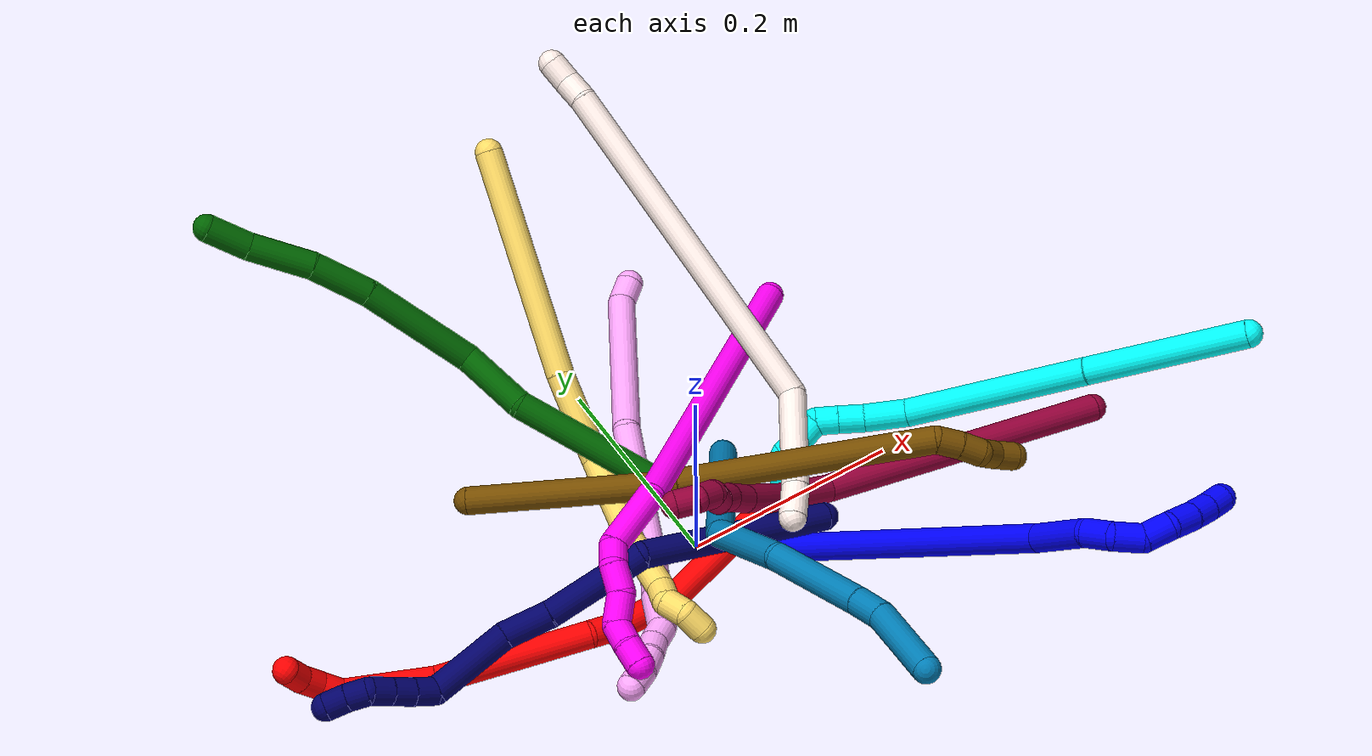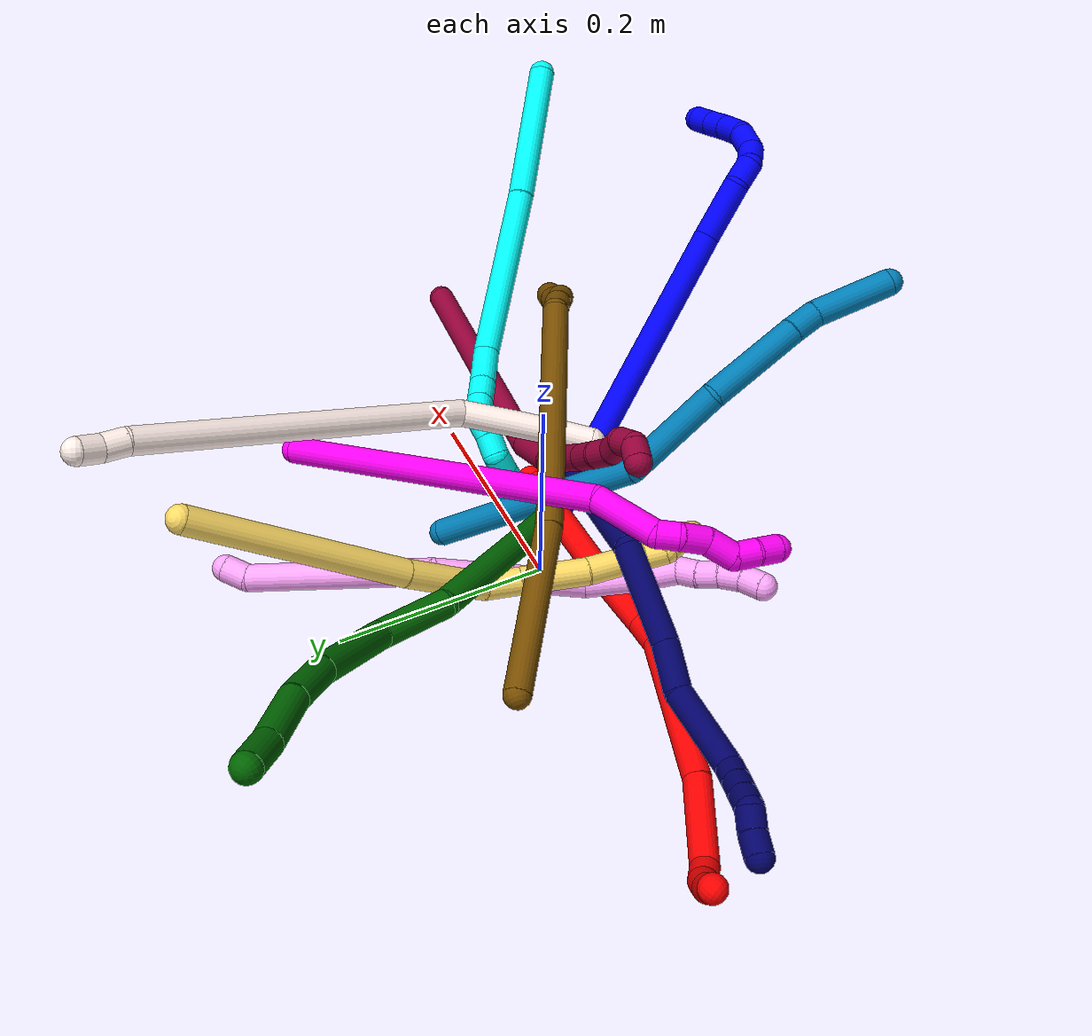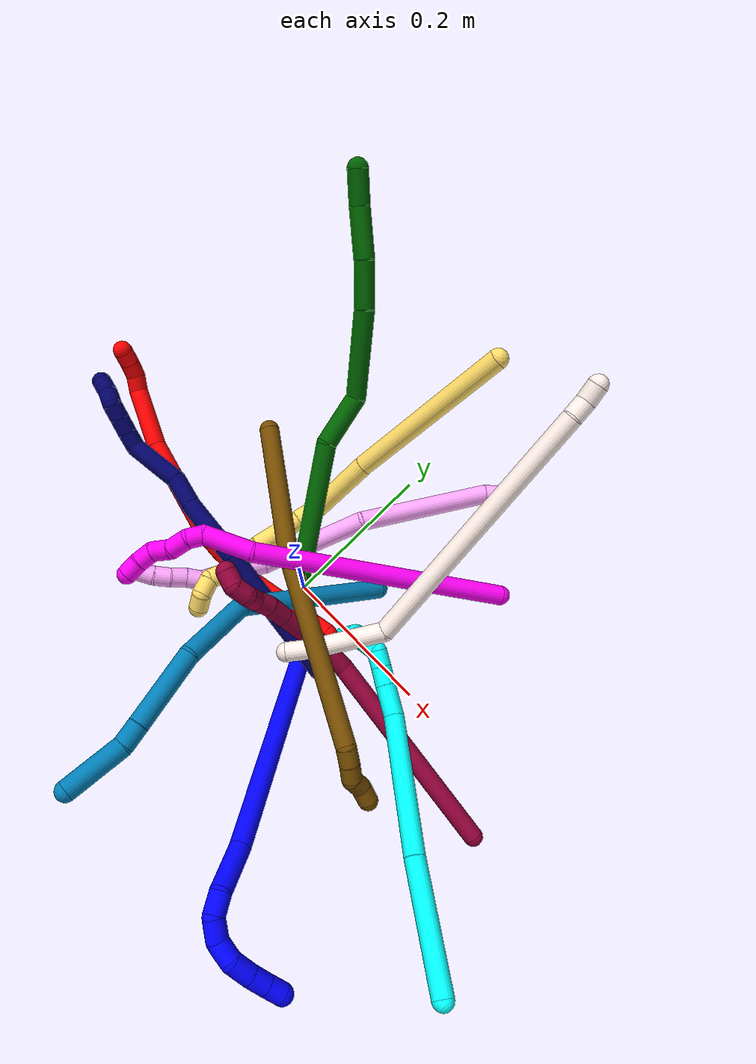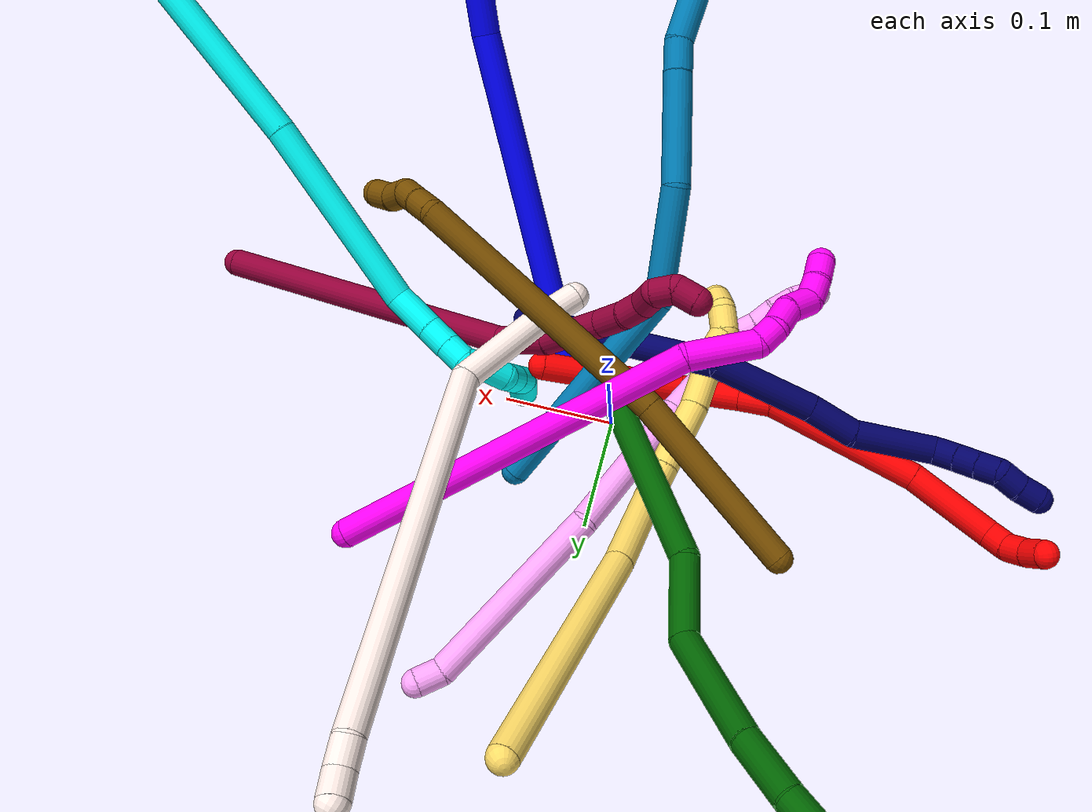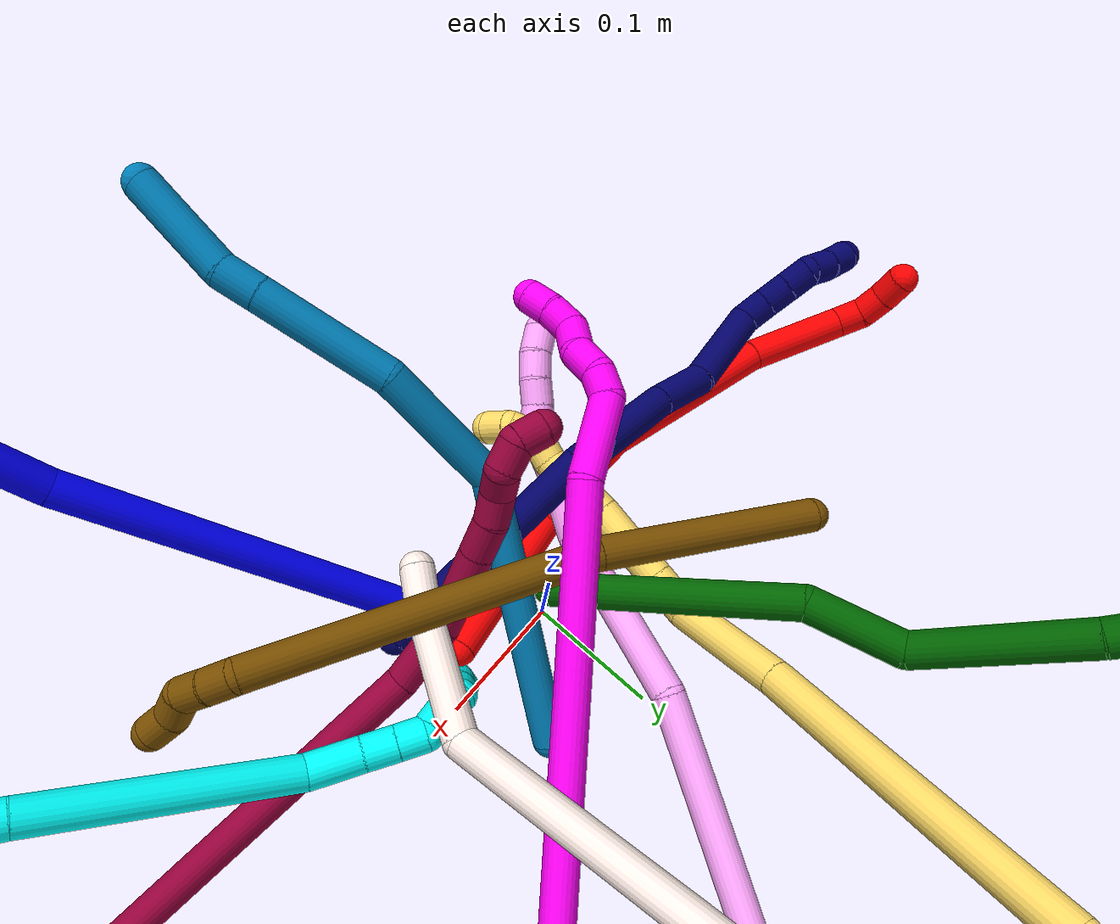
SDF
<sdf version="1.7">
 <world name="default">
  <plugin name="TubeGeneratorPlugin" filename="libtube_generator_plugin.so"/>
  <model name="photoneo_s_sensor">
   <static>1</static>
   <pose>0 0 2 1.57079 1.57079 3.14159</pose>
   <link name="link">
    <inertial><mass>0.1</mass></inertial>
    <sensor name="sensor" type="depth">
     <update_rate>30</update_rate>
     <camera>
      <horizontal_fov>1.22</horizontal_fov>
      <image><width>1920</width><height>1200</height><format>B8G8R8</format></image>
      <clip><near>0.1</near><far>4</far></clip>
      <depth_camera><output>points</output></depth_camera>
     </camera>
     <plugin name="camera_plugin" filename="libgazebo_ros_depth_camera.so">
      <baseline>0.2</baseline>
      <alwaysOn>1</alwaysOn>
      <updateRate>0.0</updateRate>
      <cameraName>camera_ir</cameraName>
      <imageTopicName>/camera/color/image_raw</imageTopicName>
      <cameraInfoTopicName>/camera/color/camera_info</cameraInfoTopicName>
      <depthImageTopicName>/camera/depth/image_raw</depthImageTopicName>
      <depthImageCameraInfoTopicName>/camera/depth/camera_info</depthImageCameraInfoTopicName>
      <pointCloudTopicName>/camera/depth/points</pointCloudTopicName>
      <frameName>fr_optical</frameName>
      <pointCloudCutoff>0.1</pointCloudCutoff>
      <pointCloudCutoffMax>2.0</pointCloudCutoffMax>
      <distortionK1>0</distortionK1>
      <distortionK2>0</distortionK2>
      <distortionK3>0</distortionK3>
      <distortionT1>0</distortionT1>
      <distortionT2>0</distortionT2>
      <CxPrime>0</CxPrime>
      <Cx>0</Cx>
      <Cy>0</Cy>
      <focalLength>0</focalLength>
      <hackBaseline>0</hackBaseline>
     </plugin>
    </sensor>
   </link>
  </model>
  <gravity>0 0 -9.8</gravity>
  <magnetic_field>6e-06 2.3e-05 -4.2e-05</magnetic_field>
  <atmosphere type="adiabatic"/>
  <physics name="default_physics" default="0" type="ode">
   <max_step_size>0.003</max_step_size>
   <real_time_factor>1</real_time_factor>
   <real_time_update_rate>1000</real_time_update_rate>
   <max_contacts>10000</max_contacts>
   <ode>
    <solver>
     <type>quick</type>
     <iters>100</iters>
     <sor>1.3</sor>
     <use_dynamic_moi_rescaling>0</use_dynamic_moi_rescaling>
    </solver>
    <constraints>
     <contact_max_correcting_vel>0</contact_max_correcting_vel>
     <contact_surface_layer>0.001</contact_surface_layer>
     <cfm>0</cfm>
     <erp>0.2</erp>
    </constraints>
   </ode>
  </physics>
  <scene><ambient>0.4 0.4 0.4 1</ambient><background>0.7 0.7 0.7 1</background><shadows>0</shadows></scene>
  <audio><device>default</device></audio>
  <spherical_coordinates>
   <surface_model>EARTH_WGS84</surface_model>
   <latitude_deg>0</latitude_deg>
   <longitude_deg>0</longitude_deg>
   <elevation>0</elevation>
   <heading_deg>0</heading_deg>
  </spherical_coordinates>
  <model name="bin">
   <static>1</static>
   <link name="bottom">
    <collision name="collision-bottom">
     <pose>0 0 -0.01 0 -0 0</pose>
     <geometry><box><size>0.8 0.6 0.02</size></box></geometry>
     <surface>
      <friction><ode><mu>100</mu><mu2>100</mu2></ode></friction>
      <contact><collide_bitmask>65535</collide_bitmask></contact>
     </surface>
    </collision>
   </link>
   <link name="west_wall">
    <collision name="collision-west_wall">
     <pose>-0.41 0 0.1 0 -0 0</pose>
     <geometry><box><size>0.02 0.6 0.2</size></box></geometry>
     <surface>
      <friction><ode><mu>100</mu><mu2>100</mu2></ode></friction>
      <contact><collide_bitmask>65535</collide_bitmask></contact>
     </surface>
    </collision>
   </link>
   <link name="east_wall">
    <collision name="collision-east_wall">
     <pose>0.41 0 0.1 0 -0 0</pose>
     <geometry><box><size>0.02 0.6 0.2</size></box></geometry>
     <surface>
      <friction><ode><mu>100</mu><mu2>100</mu2></ode></friction>
      <contact><collide_bitmask>65535</collide_bitmask></contact>
     </surface>
    </collision>
   </link>
   <link name="south_wall">
    <collision name="collision-south_wall">
     <pose>0 -0.31 0.1 0 -0 0</pose>
     <geometry><box><size>0.8 0.02 0.2</size></box></geometry>
     <surface>
      <friction><ode><mu>100</mu><mu2>100</mu2></ode></friction>
      <contact><collide_bitmask>65535</collide_bitmask></contact>
     </surface>
    </collision>
   </link>
   <link name="north_wall">
    <collision name="collision-north_wall">
     <pose>0 0.31 0.1 0 -0 0</pose>
     <geometry><box><size>0.8 0.02 0.2</size></box></geometry>
     <surface>
      <friction><ode><mu>100</mu><mu2>100</mu2></ode></friction>
      <contact><collide_bitmask>65535</collide_bitmask></contact>
     </surface>
    </collision>
   </link>
  </model>
  <model name="1">
   <static>0</static>
   <link name="1">
    <collision name="collision-cylinder-e_1_1_4">
     <pose>0.01469 -0.020997 0.14681 0.14206 0.098733 0.007031</pose>
     <geometry><cylinder><radius>0.0125</radius><length>0.298061</length></cylinder></geometry>
     <surface>
      <friction><ode><mu>1.16</mu><mu2>1.16</mu2><slip1>0</slip1><slip2>0</slip2></ode></friction>
      <contact><ode><kp>1e+06</kp><kd>1</kd><max_vel>0</max_vel><min_depth>0.001</min_depth></ode></contact>
     </surface>
    </collision>
    <visual name="visual-cylinder-e_1_1_4">
     <pose>0.01469 -0.020997 0.14681 0.14206 0.098733 0.007031</pose>
     <geometry><cylinder><radius>0.0125</radius><length>0.298061</length></cylinder></geometry>
     <material><ambient>0 0 1 1</ambient></material>
    </visual>
    <collision name="collision-cylinder-e_2_4_5">
     <pose>0.034722 -0.050012 0.320946 0.285379 0.185399 0.02671</pose>
     <geometry><cylinder><radius>0.0125</radius><length>0.057946</length></cylinder></geometry>
     <surface>
      <friction><ode><mu>1.16</mu><mu2>1.16</mu2><slip1>0</slip1><slip2>0</slip2></ode></friction>
      <contact><ode><kp>1e+06</kp><kd>1</kd><max_vel>0</max_vel><min_depth>0.001</min_depth></ode></contact>
     </surface>
    </collision>
    <visual name="visual-cylinder-e_2_4_5">
     <pose>0.034722 -0.050012 0.320946 0.285379 0.185399 0.02671</pose>
     <geometry><cylinder><radius>0.0125</radius><length>0.057946</length></cylinder></geometry>
     <material><ambient>0 0 1 1</ambient></material>
    </visual>
    <collision name="collision-cylinder-e_3_5_6">
     <pose>0.040855 -0.056942 0.361068 -0.084671 0.061662 -0.002613</pose>
     <geometry><cylinder><radius>0.0125</radius><length>0.025736</length></cylinder></geometry>
     <surface>
      <friction><ode><mu>1.16</mu><mu2>1.16</mu2><slip1>0</slip1><slip2>0</slip2></ode></friction>
      <contact><ode><kp>1e+06</kp><kd>1</kd><max_vel>0</max_vel><min_depth>0.001</min_depth></ode></contact>
     </surface>
    </collision>
    <visual name="visual-cylinder-e_3_5_6">
     <pose>0.040855 -0.056942 0.361068 -0.084671 0.061662 -0.002613</pose>
     <geometry><cylinder><radius>0.0125</radius><length>0.025736</length></cylinder></geometry>
     <material><ambient>0 0 1 1</ambient></material>
    </visual>
    <collision name="collision-cylinder-e_4_6_7">
     <pose>0.036616 -0.050254 0.384391 -0.489094 -0.399334 0.10091</pose>
     <geometry><cylinder><radius>0.0125</radius><length>0.025885</length></cylinder></geometry>
     <surface>
      <friction><ode><mu>1.16</mu><mu2>1.16</mu2><slip1>0</slip1><slip2>0</slip2></ode></friction>
      <contact><ode><kp>1e+06</kp><kd>1</kd><max_vel>0</max_vel><min_depth>0.001</min_depth></ode></contact>
     </surface>
    </collision>
    <visual name="visual-cylinder-e_4_6_7">
     <pose>0.036616 -0.050254 0.384391 -0.489094 -0.399334 0.10091</pose>
     <geometry><cylinder><radius>0.0125</radius><length>0.025885</length></cylinder></geometry>
     <material><ambient>0 0 1 1</ambient></material>
    </visual>
    <collision name="collision-cylinder-e_5_7_8">
     <pose>0.022232 -0.043344 0.402956 -0.161236 -0.854338 0.073521</pose>
     <geometry><cylinder><radius>0.0125</radius><length>0.024802</length></cylinder></geometry>
     <surface>
      <friction><ode><mu>1.16</mu><mu2>1.16</mu2><slip1>0</slip1><slip2>0</slip2></ode></friction>
      <contact><ode><kp>1e+06</kp><kd>1</kd><max_vel>0</max_vel><min_depth>0.001</min_depth></ode></contact>
     </surface>
    </collision>
    <visual name="visual-cylinder-e_5_7_8">
     <pose>0.022232 -0.043344 0.402956 -0.161236 -0.854338 0.073521</pose>
     <geometry><cylinder><radius>0.0125</radius><length>0.024802</length></cylinder></geometry>
     <material><ambient>0 0 1 1</ambient></material>
    </visual>
    <collision name="collision-cylinder-e_6_8_9">
     <pose>0.001599 -0.037132 0.414829 -0.907283 -1.0665 0.56045</pose>
     <geometry><cylinder><radius>0.0125</radius><length>0.02577</length></cylinder></geometry>
     <surface>
      <friction><ode><mu>1.16</mu><mu2>1.16</mu2><slip1>0</slip1><slip2>0</slip2></ode></friction>
      <contact><ode><kp>1e+06</kp><kd>1</kd><max_vel>0</max_vel><min_depth>0.001</min_depth></ode></contact>
     </surface>
    </collision>
    <visual name="visual-cylinder-e_6_8_9">
     <pose>0.001599 -0.037132 0.414829 -0.907283 -1.0665 0.56045</pose>
     <geometry><cylinder><radius>0.0125</radius><length>0.02577</length></cylinder></geometry>
     <material><ambient>0 0 1 1</ambient></material>
    </visual>
    <collision name="collision-cylinder-e_7_9_10">
     <pose>-0.019461 -0.028372 0.421044 -1.01745 -1.1369 0.684445</pose>
     <geometry><cylinder><radius>0.0125</radius><length>0.021556</length></cylinder></geometry>
     <surface>
      <friction><ode><mu>1.16</mu><mu2>1.16</mu2><slip1>0</slip1><slip2>0</slip2></ode></friction>
      <contact><ode><kp>1e+06</kp><kd>1</kd><max_vel>0</max_vel><min_depth>0.001</min_depth></ode></contact>
     </surface>
    </collision>
    <visual name="visual-cylinder-e_7_9_10">
     <pose>-0.019461 -0.028372 0.421044 -1.01745 -1.1369 0.684445</pose>
     <geometry><cylinder><radius>0.0125</radius><length>0.021556</length></cylinder></geometry>
     <material><ambient>0 0 1 1</ambient></material>
    </visual>
    <collision name="collision-cylinder-e_8_10_2">
     <pose>-0.038668 -0.021519 0.42557 -0.949847 -1.19812 0.675231</pose>
     <geometry><cylinder><radius>0.0125</radius><length>0.020246</length></cylinder></geometry>
     <surface>
      <friction><ode><mu>1.16</mu><mu2>1.16</mu2><slip1>0</slip1><slip2>0</slip2></ode></friction>
      <contact><ode><kp>1e+06</kp><kd>1</kd><max_vel>0</max_vel><min_depth>0.001</min_depth></ode></contact>
     </surface>
    </collision>
    <visual name="visual-cylinder-e_8_10_2">
     <pose>-0.038668 -0.021519 0.42557 -0.949847 -1.19812 0.675231</pose>
     <geometry><cylinder><radius>0.0125</radius><length>0.020246</length></cylinder></geometry>
     <material><ambient>0 0 1 1</ambient></material>
    </visual>
    <collision name="collision-sphere-2">
     <pose>-0.048096 -0.018521 0.427714 0 -0 0</pose>
     <geometry><sphere><radius>0.0125</radius></sphere></geometry>
     <surface>
      <friction><ode><mu>1.16</mu><mu2>1.16</mu2><slip1>0</slip1><slip2>0</slip2></ode></friction>
      <contact><ode><kp>1e+06</kp><kd>1</kd><max_vel>0</max_vel><min_depth>0.001</min_depth></ode></contact>
     </surface>
    </collision>
    <visual name="visual-sphere-2">
     <pose>-0.048096 -0.018521 0.427714 0 -0 0</pose>
     <geometry><sphere><radius>0.0125</radius></sphere></geometry>
     <material><ambient>0 0 1 1</ambient></material>
    </visual>
    <collision name="collision-sphere-10">
     <pose>-0.02924 -0.024517 0.423426 0 -0 0</pose>
     <geometry><sphere><radius>0.0125</radius></sphere></geometry>
     <surface>
      <friction><ode><mu>1.16</mu><mu2>1.16</mu2><slip1>0</slip1><slip2>0</slip2></ode></friction>
      <contact><ode><kp>1e+06</kp><kd>1</kd><max_vel>0</max_vel><min_depth>0.001</min_depth></ode></contact>
     </surface>
    </collision>
    <visual name="visual-sphere-10">
     <pose>-0.02924 -0.024517 0.423426 0 -0 0</pose>
     <geometry><sphere><radius>0.0125</radius></sphere></geometry>
     <material><ambient>0 0 1 1</ambient></material>
    </visual>
    <collision name="collision-sphere-9">
     <pose>-0.009682 -0.032227 0.418663 0 -0 0</pose>
     <geometry><sphere><radius>0.0125</radius></sphere></geometry>
     <surface>
      <friction><ode><mu>1.16</mu><mu2>1.16</mu2><slip1>0</slip1><slip2>0</slip2></ode></friction>
      <contact><ode><kp>1e+06</kp><kd>1</kd><max_vel>0</max_vel><min_depth>0.001</min_depth></ode></contact>
     </surface>
    </collision>
    <visual name="visual-sphere-9">
     <pose>-0.009682 -0.032227 0.418663 0 -0 0</pose>
     <geometry><sphere><radius>0.0125</radius></sphere></geometry>
     <material><ambient>0 0 1 1</ambient></material>
    </visual>
    <collision name="collision-sphere-4">
     <pose>0.029381 -0.041995 0.293621 0 -0 0</pose>
     <geometry><sphere><radius>0.0125</radius></sphere></geometry>
     <surface>
      <friction><ode><mu>1.16</mu><mu2>1.16</mu2><slip1>0</slip1><slip2>0</slip2></ode></friction>
      <contact><ode><kp>1e+06</kp><kd>1</kd><max_vel>0</max_vel><min_depth>0.001</min_depth></ode></contact>
     </surface>
    </collision>
    <visual name="visual-sphere-4">
     <pose>0.029381 -0.041995 0.293621 0 -0 0</pose>
     <geometry><sphere><radius>0.0125</radius></sphere></geometry>
     <material><ambient>0 0 1 1</ambient></material>
    </visual>
    <collision name="collision-sphere-1">
     <geometry><sphere><radius>0.0125</radius></sphere></geometry>
     <surface>
      <friction><ode><mu>1.16</mu><mu2>1.16</mu2><slip1>0</slip1><slip2>0</slip2></ode></friction>
      <contact><ode><kp>1e+06</kp><kd>1</kd><max_vel>0</max_vel><min_depth>0.001</min_depth></ode></contact>
     </surface>
    </collision>
    <visual name="visual-sphere-1">
     <geometry><sphere><radius>0.0125</radius></sphere></geometry>
     <material><ambient>0 0 1 1</ambient></material>
    </visual>
    <collision name="collision-sphere-8">
     <pose>0.01288 -0.042037 0.410994 0 -0 0</pose>
     <geometry><sphere><radius>0.0125</radius></sphere></geometry>
     <surface>
      <friction><ode><mu>1.16</mu><mu2>1.16</mu2><slip1>0</slip1><slip2>0</slip2></ode></friction>
      <contact><ode><kp>1e+06</kp><kd>1</kd><max_vel>0</max_vel><min_depth>0.001</min_depth></ode></contact>
     </surface>
    </collision>
    <visual name="visual-sphere-8">
     <pose>0.01288 -0.042037 0.410994 0 -0 0</pose>
     <geometry><sphere><radius>0.0125</radius></sphere></geometry>
     <material><ambient>0 0 1 1</ambient></material>
    </visual>
    <collision name="collision-sphere-5">
     <pose>0.040062 -0.058028 0.34827 0 -0 0</pose>
     <geometry><sphere><radius>0.0125</radius></sphere></geometry>
     <surface>
      <friction><ode><mu>1.16</mu><mu2>1.16</mu2><slip1>0</slip1><slip2>0</slip2></ode></friction>
      <contact><ode><kp>1e+06</kp><kd>1</kd><max_vel>0</max_vel><min_depth>0.001</min_depth></ode></contact>
     </surface>
    </collision>
    <visual name="visual-sphere-5">
     <pose>0.040062 -0.058028 0.34827 0 -0 0</pose>
     <geometry><sphere><radius>0.0125</radius></sphere></geometry>
     <material><ambient>0 0 1 1</ambient></material>
    </visual>
    <collision name="collision-sphere-6">
     <pose>0.041648 -0.055856 0.373865 0 -0 0</pose>
     <geometry><sphere><radius>0.0125</radius></sphere></geometry>
     <surface>
      <friction><ode><mu>1.16</mu><mu2>1.16</mu2><slip1>0</slip1><slip2>0</slip2></ode></friction>
      <contact><ode><kp>1e+06</kp><kd>1</kd><max_vel>0</max_vel><min_depth>0.001</min_depth></ode></contact>
     </surface>
    </collision>
    <visual name="visual-sphere-6">
     <pose>0.041648 -0.055856 0.373865 0 -0 0</pose>
     <geometry><sphere><radius>0.0125</radius></sphere></geometry>
     <material><ambient>0 0 1 1</ambient></material>
    </visual>
    <collision name="collision-sphere-7">
     <pose>0.031584 -0.044651 0.394917 0 -0 0</pose>
     <geometry><sphere><radius>0.0125</radius></sphere></geometry>
     <surface>
      <friction><ode><mu>1.16</mu><mu2>1.16</mu2><slip1>0</slip1><slip2>0</slip2></ode></friction>
      <contact><ode><kp>1e+06</kp><kd>1</kd><max_vel>0</max_vel><min_depth>0.001</min_depth></ode></contact>
     </surface>
    </collision>
    <visual name="visual-sphere-7">
     <pose>0.031584 -0.044651 0.394917 0 -0 0</pose>
     <geometry><sphere><radius>0.0125</radius></sphere></geometry>
     <material><ambient>0 0 1 1</ambient></material>
    </visual>
    <inertial>
     <pose>0.01556 -0.030004 0.239948 0 -0 0</pose>
     <mass>0.5</mass>
     <inertia>
      <ixx>0.002248</ixx>
      <ixy>0</ixy>
      <ixz>0</ixz>
      <iyy>0.002242</iyy>
      <iyz>0</iyz>
      <izz>0.000133</izz>
     </inertia>
    </inertial>
   </link>
   <pose>0.053611 -0.046879 0.011493 -1.1229 -0.090207 -2.56875</pose>
  </model>
  <model name="2">
   <static>0</static>
   <link name="2">
    <collision name="collision-cylinder-e_1_1_4">
     <pose>-0.016483 -0.006897 0.062198 0.110441 -0.257541 -0.014315</pose>
     <geometry><cylinder><radius>0.0125</radius><length>0.129426</length></cylinder></geometry>
     <surface>
      <friction><ode><mu>1.16</mu><mu2>1.16</mu2><slip1>0</slip1><slip2>0</slip2></ode></friction>
      <contact><ode><kp>1e+06</kp><kd>1</kd><max_vel>0</max_vel><min_depth>0.001</min_depth></ode></contact>
     </surface>
    </collision>
    <visual name="visual-cylinder-e_1_1_4">
     <pose>-0.016483 -0.006897 0.062198 0.110441 -0.257541 -0.014315</pose>
     <geometry><cylinder><radius>0.0125</radius><length>0.129426</length></cylinder></geometry>
     <material><ambient>1 0 0 1</ambient></material>
    </visual>
    <collision name="collision-cylinder-e_2_4_5">
     <pose>-0.044584 -0.007371 0.148681 -0.258587 -0.43321 0.057208</pose>
     <geometry><cylinder><radius>0.0125</radius><length>0.055356</length></cylinder></geometry>
     <surface>
      <friction><ode><mu>1.16</mu><mu2>1.16</mu2><slip1>0</slip1><slip2>0</slip2></ode></friction>
      <contact><ode><kp>1e+06</kp><kd>1</kd><max_vel>0</max_vel><min_depth>0.001</min_depth></ode></contact>
     </surface>
    </collision>
    <visual name="visual-cylinder-e_2_4_5">
     <pose>-0.044584 -0.007371 0.148681 -0.258587 -0.43321 0.057208</pose>
     <geometry><cylinder><radius>0.0125</radius><length>0.055356</length></cylinder></geometry>
     <material><ambient>1 0 0 1</ambient></material>
    </visual>
    <collision name="collision-cylinder-e_3_5_6">
     <pose>-0.064183 0.004507 0.185072 -0.423331 -0.541164 0.11907</pose>
     <geometry><cylinder><radius>0.0125</radius><length>0.03098</length></cylinder></geometry>
     <surface>
      <friction><ode><mu>1.16</mu><mu2>1.16</mu2><slip1>0</slip1><slip2>0</slip2></ode></friction>
      <contact><ode><kp>1e+06</kp><kd>1</kd><max_vel>0</max_vel><min_depth>0.001</min_depth></ode></contact>
     </surface>
    </collision>
    <visual name="visual-cylinder-e_3_5_6">
     <pose>-0.064183 0.004507 0.185072 -0.423331 -0.541164 0.11907</pose>
     <geometry><cylinder><radius>0.0125</radius><length>0.03098</length></cylinder></geometry>
     <material><ambient>1 0 0 1</ambient></material>
    </visual>
    <collision name="collision-cylinder-e_4_6_7">
     <pose>-0.118391 0.012034 0.249811 -0.039355 -0.720318 0.014822</pose>
     <geometry><cylinder><radius>0.0125</radius><length>0.140169</length></cylinder></geometry>
     <surface>
      <friction><ode><mu>1.16</mu><mu2>1.16</mu2><slip1>0</slip1><slip2>0</slip2></ode></friction>
      <contact><ode><kp>1e+06</kp><kd>1</kd><max_vel>0</max_vel><min_depth>0.001</min_depth></ode></contact>
     </surface>
    </collision>
    <visual name="visual-cylinder-e_4_6_7">
     <pose>-0.118391 0.012034 0.249811 -0.039355 -0.720318 0.014822</pose>
     <geometry><cylinder><radius>0.0125</radius><length>0.140169</length></cylinder></geometry>
     <material><ambient>1 0 0 1</ambient></material>
    </visual>
    <collision name="collision-cylinder-e_5_7_8">
     <pose>-0.196631 0.013745 0.328034 0.014114 -0.896392 -0.006786</pose>
     <geometry><cylinder><radius>0.0125</radius><length>0.081964</length></cylinder></geometry>
     <surface>
      <friction><ode><mu>1.16</mu><mu2>1.16</mu2><slip1>0</slip1><slip2>0</slip2></ode></friction>
      <contact><ode><kp>1e+06</kp><kd>1</kd><max_vel>0</max_vel><min_depth>0.001</min_depth></ode></contact>
     </surface>
    </collision>
    <visual name="visual-cylinder-e_5_7_8">
     <pose>-0.196631 0.013745 0.328034 0.014114 -0.896392 -0.006786</pose>
     <geometry><cylinder><radius>0.0125</radius><length>0.081964</length></cylinder></geometry>
     <material><ambient>1 0 0 1</ambient></material>
    </visual>
    <collision name="collision-cylinder-e_6_8_9">
     <pose>-0.237722 0.018271 0.356886 -0.981888 -0.99644 0.566027</pose>
     <geometry><cylinder><radius>0.0125</radius><length>0.021633</length></cylinder></geometry>
     <surface>
      <friction><ode><mu>1.16</mu><mu2>1.16</mu2><slip1>0</slip1><slip2>0</slip2></ode></friction>
      <contact><ode><kp>1e+06</kp><kd>1</kd><max_vel>0</max_vel><min_depth>0.001</min_depth></ode></contact>
     </surface>
    </collision>
    <visual name="visual-cylinder-e_6_8_9">
     <pose>-0.237722 0.018271 0.356886 -0.981888 -0.99644 0.566027</pose>
     <geometry><cylinder><radius>0.0125</radius><length>0.021633</length></cylinder></geometry>
     <material><ambient>1 0 0 1</ambient></material>
    </visual>
    <collision name="collision-cylinder-e_7_9_10">
     <pose>-0.252983 0.030297 0.363691 -1.11041 -0.659582 0.418428</pose>
     <geometry><cylinder><radius>0.0125</radius><length>0.02017</length></cylinder></geometry>
     <surface>
      <friction><ode><mu>1.16</mu><mu2>1.16</mu2><slip1>0</slip1><slip2>0</slip2></ode></friction>
      <contact><ode><kp>1e+06</kp><kd>1</kd><max_vel>0</max_vel><min_depth>0.001</min_depth></ode></contact>
     </surface>
    </collision>
    <visual name="visual-cylinder-e_7_9_10">
     <pose>-0.252983 0.030297 0.363691 -1.11041 -0.659582 0.418428</pose>
     <geometry><cylinder><radius>0.0125</radius><length>0.02017</length></cylinder></geometry>
     <material><ambient>1 0 0 1</ambient></material>
    </visual>
    <collision name="collision-cylinder-e_8_10_2">
     <pose>-0.263932 0.046089 0.369563 -1.3076 -0.489087 0.37784</pose>
     <geometry><cylinder><radius>0.0125</radius><length>0.020302</length></cylinder></geometry>
     <surface>
      <friction><ode><mu>1.16</mu><mu2>1.16</mu2><slip1>0</slip1><slip2>0</slip2></ode></friction>
      <contact><ode><kp>1e+06</kp><kd>1</kd><max_vel>0</max_vel><min_depth>0.001</min_depth></ode></contact>
     </surface>
    </collision>
    <visual name="visual-cylinder-e_8_10_2">
     <pose>-0.263932 0.046089 0.369563 -1.3076 -0.489087 0.37784</pose>
     <geometry><cylinder><radius>0.0125</radius><length>0.020302</length></cylinder></geometry>
     <material><ambient>1 0 0 1</ambient></material>
    </visual>
    <collision name="collision-sphere-2">
     <pose>-0.268701 0.054741 0.371894 0 -0 0</pose>
     <geometry><sphere><radius>0.0125</radius></sphere></geometry>
     <surface>
      <friction><ode><mu>1.16</mu><mu2>1.16</mu2><slip1>0</slip1><slip2>0</slip2></ode></friction>
      <contact><ode><kp>1e+06</kp><kd>1</kd><max_vel>0</max_vel><min_depth>0.001</min_depth></ode></contact>
     </surface>
    </collision>
    <visual name="visual-sphere-2">
     <pose>-0.268701 0.054741 0.371894 0 -0 0</pose>
     <geometry><sphere><radius>0.0125</radius></sphere></geometry>
     <material><ambient>1 0 0 1</ambient></material>
    </visual>
    <collision name="collision-sphere-10">
     <pose>-0.259163 0.037437 0.367231 0 -0 0</pose>
     <geometry><sphere><radius>0.0125</radius></sphere></geometry>
     <surface>
      <friction><ode><mu>1.16</mu><mu2>1.16</mu2><slip1>0</slip1><slip2>0</slip2></ode></friction>
      <contact><ode><kp>1e+06</kp><kd>1</kd><max_vel>0</max_vel><min_depth>0.001</min_depth></ode></contact>
     </surface>
    </collision>
    <visual name="visual-sphere-10">
     <pose>-0.259163 0.037437 0.367231 0 -0 0</pose>
     <geometry><sphere><radius>0.0125</radius></sphere></geometry>
     <material><ambient>1 0 0 1</ambient></material>
    </visual>
    <collision name="collision-sphere-9">
     <pose>-0.246803 0.023157 0.36015 0 -0 0</pose>
     <geometry><sphere><radius>0.0125</radius></sphere></geometry>
     <surface>
      <friction><ode><mu>1.16</mu><mu2>1.16</mu2><slip1>0</slip1><slip2>0</slip2></ode></friction>
      <contact><ode><kp>1e+06</kp><kd>1</kd><max_vel>0</max_vel><min_depth>0.001</min_depth></ode></contact>
     </surface>
    </collision>
    <visual name="visual-sphere-9">
     <pose>-0.246803 0.023157 0.36015 0 -0 0</pose>
     <geometry><sphere><radius>0.0125</radius></sphere></geometry>
     <material><ambient>1 0 0 1</ambient></material>
    </visual>
    <collision name="collision-sphere-4">
     <pose>-0.032965 -0.013794 0.124395 0 -0 0</pose>
     <geometry><sphere><radius>0.0125</radius></sphere></geometry>
     <surface>
      <friction><ode><mu>1.16</mu><mu2>1.16</mu2><slip1>0</slip1><slip2>0</slip2></ode></friction>
      <contact><ode><kp>1e+06</kp><kd>1</kd><max_vel>0</max_vel><min_depth>0.001</min_depth></ode></contact>
     </surface>
    </collision>
    <visual name="visual-sphere-4">
     <pose>-0.032965 -0.013794 0.124395 0 -0 0</pose>
     <geometry><sphere><radius>0.0125</radius></sphere></geometry>
     <material><ambient>1 0 0 1</ambient></material>
    </visual>
    <collision name="collision-sphere-1">
     <geometry><sphere><radius>0.0125</radius></sphere></geometry>
     <surface>
      <friction><ode><mu>1.16</mu><mu2>1.16</mu2><slip1>0</slip1><slip2>0</slip2></ode></friction>
      <contact><ode><kp>1e+06</kp><kd>1</kd><max_vel>0</max_vel><min_depth>0.001</min_depth></ode></contact>
     </surface>
    </collision>
    <visual name="visual-sphere-1">
     <geometry><sphere><radius>0.0125</radius></sphere></geometry>
     <material><ambient>1 0 0 1</ambient></material>
    </visual>
    <collision name="collision-sphere-8">
     <pose>-0.228641 0.013384 0.353621 0 -0 0</pose>
     <geometry><sphere><radius>0.0125</radius></sphere></geometry>
     <surface>
      <friction><ode><mu>1.16</mu><mu2>1.16</mu2><slip1>0</slip1><slip2>0</slip2></ode></friction>
      <contact><ode><kp>1e+06</kp><kd>1</kd><max_vel>0</max_vel><min_depth>0.001</min_depth></ode></contact>
     </surface>
    </collision>
    <visual name="visual-sphere-8">
     <pose>-0.228641 0.013384 0.353621 0 -0 0</pose>
     <geometry><sphere><radius>0.0125</radius></sphere></geometry>
     <material><ambient>1 0 0 1</ambient></material>
    </visual>
    <collision name="collision-sphere-5">
     <pose>-0.056203 -0.000947 0.172967 0 -0 0</pose>
     <geometry><sphere><radius>0.0125</radius></sphere></geometry>
     <surface>
      <friction><ode><mu>1.16</mu><mu2>1.16</mu2><slip1>0</slip1><slip2>0</slip2></ode></friction>
      <contact><ode><kp>1e+06</kp><kd>1</kd><max_vel>0</max_vel><min_depth>0.001</min_depth></ode></contact>
     </surface>
    </collision>
    <visual name="visual-sphere-5">
     <pose>-0.056203 -0.000947 0.172967 0 -0 0</pose>
     <geometry><sphere><radius>0.0125</radius></sphere></geometry>
     <material><ambient>1 0 0 1</ambient></material>
    </visual>
    <collision name="collision-sphere-6">
     <pose>-0.072162 0.009961 0.197177 0 -0 0</pose>
     <geometry><sphere><radius>0.0125</radius></sphere></geometry>
     <surface>
      <friction><ode><mu>1.16</mu><mu2>1.16</mu2><slip1>0</slip1><slip2>0</slip2></ode></friction>
      <contact><ode><kp>1e+06</kp><kd>1</kd><max_vel>0</max_vel><min_depth>0.001</min_depth></ode></contact>
     </surface>
    </collision>
    <visual name="visual-sphere-6">
     <pose>-0.072162 0.009961 0.197177 0 -0 0</pose>
     <geometry><sphere><radius>0.0125</radius></sphere></geometry>
     <material><ambient>1 0 0 1</ambient></material>
    </visual>
    <collision name="collision-sphere-7">
     <pose>-0.164621 0.014106 0.302446 0 -0 0</pose>
     <geometry><sphere><radius>0.0125</radius></sphere></geometry>
     <surface>
      <friction><ode><mu>1.16</mu><mu2>1.16</mu2><slip1>0</slip1><slip2>0</slip2></ode></friction>
      <contact><ode><kp>1e+06</kp><kd>1</kd><max_vel>0</max_vel><min_depth>0.001</min_depth></ode></contact>
     </surface>
    </collision>
    <visual name="visual-sphere-7">
     <pose>-0.164621 0.014106 0.302446 0 -0 0</pose>
     <geometry><sphere><radius>0.0125</radius></sphere></geometry>
     <material><ambient>1 0 0 1</ambient></material>
    </visual>
    <inertial>
     <pose>-0.109809 0.007189 0.212951 0 -0 0</pose>
     <mass>0.5</mass>
     <inertia>
      <ixx>0.000389</ixx>
      <ixy>0</ixy>
      <ixz>0</ixz>
      <iyy>0.000498</iyy>
      <iyz>0</iyz>
      <izz>0.000287</izz>
     </inertia>
    </inertial>
   </link>
   <pose>0.068594 -0.022581 0.046968 1.78169 0.114303 -1.09341</pose>
  </model>
  <model name="3">
   <static>0</static>
   <link name="3">
    <collision name="collision-cylinder-e_1_1_4">
     <pose>-0.018677 -0.027858 -0.065253 2.7381 -0.257404 -1.12832</pose>
     <geometry><cylinder><radius>0.0125</radius><length>0.146736</length></cylinder></geometry>
     <surface>
      <friction><ode><mu>1.16</mu><mu2>1.16</mu2><slip1>0</slip1><slip2>0</slip2></ode></friction>
      <contact><ode><kp>1e+06</kp><kd>1</kd><max_vel>0</max_vel><min_depth>0.001</min_depth></ode></contact>
     </surface>
    </collision>
    <visual name="visual-cylinder-e_1_1_4">
     <pose>-0.018677 -0.027858 -0.065253 2.7381 -0.257404 -1.12832</pose>
     <geometry><cylinder><radius>0.0125</radius><length>0.146736</length></cylinder></geometry>
     <material><ambient>0.003922 1 0.996078 1</ambient></material>
    </visual>
    <collision name="collision-cylinder-e_2_4_5">
     <pose>-0.065976 -0.085598 -0.205381 2.76186 -0.341143 -1.46151</pose>
     <geometry><cylinder><radius>0.0125</radius><length>0.171094</length></cylinder></geometry>
     <surface>
      <friction><ode><mu>1.16</mu><mu2>1.16</mu2><slip1>0</slip1><slip2>0</slip2></ode></friction>
      <contact><ode><kp>1e+06</kp><kd>1</kd><max_vel>0</max_vel><min_depth>0.001</min_depth></ode></contact>
     </surface>
    </collision>
    <visual name="visual-cylinder-e_2_4_5">
     <pose>-0.065976 -0.085598 -0.205381 2.76186 -0.341143 -1.46151</pose>
     <geometry><cylinder><radius>0.0125</radius><length>0.171094</length></cylinder></geometry>
     <material><ambient>0.003922 1 0.996078 1</ambient></material>
    </visual>
    <collision name="collision-cylinder-e_3_5_6">
     <pose>-0.095419 -0.125686 -0.296745 2.58734 -0.042391 -0.148777</pose>
     <geometry><cylinder><radius>0.0125</radius><length>0.03882</length></cylinder></geometry>
     <surface>
      <friction><ode><mu>1.16</mu><mu2>1.16</mu2><slip1>0</slip1><slip2>0</slip2></ode></friction>
      <contact><ode><kp>1e+06</kp><kd>1</kd><max_vel>0</max_vel><min_depth>0.001</min_depth></ode></contact>
     </surface>
    </collision>
    <visual name="visual-cylinder-e_3_5_6">
     <pose>-0.095419 -0.125686 -0.296745 2.58734 -0.042391 -0.148777</pose>
     <geometry><cylinder><radius>0.0125</radius><length>0.03882</length></cylinder></geometry>
     <material><ambient>0.003922 1 0.996078 1</ambient></material>
    </visual>
    <collision name="collision-cylinder-e_4_6_7">
     <pose>-0.096244 -0.142754 -0.322582 2.50845 -0.000184 -0.000561</pose>
     <geometry><cylinder><radius>0.0125</radius><length>0.023192</length></cylinder></geometry>
     <surface>
      <friction><ode><mu>1.16</mu><mu2>1.16</mu2><slip1>0</slip1><slip2>0</slip2></ode></friction>
      <contact><ode><kp>1e+06</kp><kd>1</kd><max_vel>0</max_vel><min_depth>0.001</min_depth></ode></contact>
     </surface>
    </collision>
    <visual name="visual-cylinder-e_4_6_7">
     <pose>-0.096244 -0.142754 -0.322582 2.50845 -0.000184 -0.000561</pose>
     <geometry><cylinder><radius>0.0125</radius><length>0.023192</length></cylinder></geometry>
     <material><ambient>0.003922 1 0.996078 1</ambient></material>
    </visual>
    <collision name="collision-cylinder-e_5_7_8">
     <pose>-0.096125 -0.155409 -0.340122 2.52595 0.01208 0.037991</pose>
     <geometry><cylinder><radius>0.0125</radius><length>0.020069</length></cylinder></geometry>
     <surface>
      <friction><ode><mu>1.16</mu><mu2>1.16</mu2><slip1>0</slip1><slip2>0</slip2></ode></friction>
      <contact><ode><kp>1e+06</kp><kd>1</kd><max_vel>0</max_vel><min_depth>0.001</min_depth></ode></contact>
     </surface>
    </collision>
    <visual name="visual-cylinder-e_5_7_8">
     <pose>-0.096125 -0.155409 -0.340122 2.52595 0.01208 0.037991</pose>
     <geometry><cylinder><radius>0.0125</radius><length>0.020069</length></cylinder></geometry>
     <material><ambient>0.003922 1 0.996078 1</ambient></material>
    </visual>
    <collision name="collision-cylinder-e_6_8_9">
     <pose>-0.094594 -0.159812 -0.358126 -3.00068 0.141331 -1.57377</pose>
     <geometry><cylinder><radius>0.0125</radius><length>0.02002</length></cylinder></geometry>
     <surface>
      <friction><ode><mu>1.16</mu><mu2>1.16</mu2><slip1>0</slip1><slip2>0</slip2></ode></friction>
      <contact><ode><kp>1e+06</kp><kd>1</kd><max_vel>0</max_vel><min_depth>0.001</min_depth></ode></contact>
     </surface>
    </collision>
    <visual name="visual-cylinder-e_6_8_9">
     <pose>-0.094594 -0.159812 -0.358126 -3.00068 0.141331 -1.57377</pose>
     <geometry><cylinder><radius>0.0125</radius><length>0.02002</length></cylinder></geometry>
     <material><ambient>0.003922 1 0.996078 1</ambient></material>
    </visual>
    <collision name="collision-cylinder-e_7_9_10">
     <pose>-0.09326 -0.157268 -0.377883 -3.02628 -0.007594 0.131381</pose>
     <geometry><cylinder><radius>0.0125</radius><length>0.020024</length></cylinder></geometry>
     <surface>
      <friction><ode><mu>1.16</mu><mu2>1.16</mu2><slip1>0</slip1><slip2>0</slip2></ode></friction>
      <contact><ode><kp>1e+06</kp><kd>1</kd><max_vel>0</max_vel><min_depth>0.001</min_depth></ode></contact>
     </surface>
    </collision>
    <visual name="visual-cylinder-e_7_9_10">
     <pose>-0.09326 -0.157268 -0.377883 -3.02628 -0.007594 0.131381</pose>
     <geometry><cylinder><radius>0.0125</radius><length>0.020024</length></cylinder></geometry>
     <material><ambient>0.003922 1 0.996078 1</ambient></material>
    </visual>
    <collision name="collision-cylinder-e_8_10_11">
     <pose>-0.095989 -0.14889 -0.394217 -2.29479 -0.268394 0.582146</pose>
     <geometry><cylinder><radius>0.0125</radius><length>0.020007</length></cylinder></geometry>
     <surface>
      <friction><ode><mu>1.16</mu><mu2>1.16</mu2><slip1>0</slip1><slip2>0</slip2></ode></friction>
      <contact><ode><kp>1e+06</kp><kd>1</kd><max_vel>0</max_vel><min_depth>0.001</min_depth></ode></contact>
     </surface>
    </collision>
    <visual name="visual-cylinder-e_8_10_11">
     <pose>-0.095989 -0.14889 -0.394217 -2.29479 -0.268394 0.582146</pose>
     <geometry><cylinder><radius>0.0125</radius><length>0.020007</length></cylinder></geometry>
     <material><ambient>0.003922 1 0.996078 1</ambient></material>
    </visual>
    <collision name="collision-cylinder-e_9_11_12">
     <pose>-0.101208 -0.134349 -0.406934 -2.28391 -0.259372 0.555729</pose>
     <geometry><cylinder><radius>0.0125</radius><length>0.020014</length></cylinder></geometry>
     <surface>
      <friction><ode><mu>1.16</mu><mu2>1.16</mu2><slip1>0</slip1><slip2>0</slip2></ode></friction>
      <contact><ode><kp>1e+06</kp><kd>1</kd><max_vel>0</max_vel><min_depth>0.001</min_depth></ode></contact>
     </surface>
    </collision>
    <visual name="visual-cylinder-e_9_11_12">
     <pose>-0.101208 -0.134349 -0.406934 -2.28391 -0.259372 0.555729</pose>
     <geometry><cylinder><radius>0.0125</radius><length>0.020014</length></cylinder></geometry>
     <material><ambient>0.003922 1 0.996078 1</ambient></material>
    </visual>
    <collision name="collision-cylinder-e_10_12_2">
     <pose>-0.111353 -0.122933 -0.418359 -2.46421 -0.858653 1.82991</pose>
     <geometry><cylinder><radius>0.0125</radius><length>0.020024</length></cylinder></geometry>
     <surface>
      <friction><ode><mu>1.16</mu><mu2>1.16</mu2><slip1>0</slip1><slip2>0</slip2></ode></friction>
      <contact><ode><kp>1e+06</kp><kd>1</kd><max_vel>0</max_vel><min_depth>0.001</min_depth></ode></contact>
     </surface>
    </collision>
    <visual name="visual-cylinder-e_10_12_2">
     <pose>-0.111353 -0.122933 -0.418359 -2.46421 -0.858653 1.82991</pose>
     <geometry><cylinder><radius>0.0125</radius><length>0.020024</length></cylinder></geometry>
     <material><ambient>0.003922 1 0.996078 1</ambient></material>
    </visual>
    <collision name="collision-sphere-2">
     <pose>-0.118932 -0.118833 -0.423457 0 -0 0</pose>
     <geometry><sphere><radius>0.0125</radius></sphere></geometry>
     <surface>
      <friction><ode><mu>1.16</mu><mu2>1.16</mu2><slip1>0</slip1><slip2>0</slip2></ode></friction>
      <contact><ode><kp>1e+06</kp><kd>1</kd><max_vel>0</max_vel><min_depth>0.001</min_depth></ode></contact>
     </surface>
    </collision>
    <visual name="visual-sphere-2">
     <pose>-0.118932 -0.118833 -0.423457 0 -0 0</pose>
     <geometry><sphere><radius>0.0125</radius></sphere></geometry>
     <material><ambient>0.003922 1 0.996078 1</ambient></material>
    </visual>
    <collision name="collision-sphere-12">
     <pose>-0.103774 -0.127034 -0.413261 0 -0 0</pose>
     <geometry><sphere><radius>0.0125</radius></sphere></geometry>
     <surface>
      <friction><ode><mu>1.16</mu><mu2>1.16</mu2><slip1>0</slip1><slip2>0</slip2></ode></friction>
      <contact><ode><kp>1e+06</kp><kd>1</kd><max_vel>0</max_vel><min_depth>0.001</min_depth></ode></contact>
     </surface>
    </collision>
    <visual name="visual-sphere-12">
     <pose>-0.103774 -0.127034 -0.413261 0 -0 0</pose>
     <geometry><sphere><radius>0.0125</radius></sphere></geometry>
     <material><ambient>0.003922 1 0.996078 1</ambient></material>
    </visual>
    <collision name="collision-sphere-11">
     <pose>-0.098641 -0.141664 -0.400606 0 -0 0</pose>
     <geometry><sphere><radius>0.0125</radius></sphere></geometry>
     <surface>
      <friction><ode><mu>1.16</mu><mu2>1.16</mu2><slip1>0</slip1><slip2>0</slip2></ode></friction>
      <contact><ode><kp>1e+06</kp><kd>1</kd><max_vel>0</max_vel><min_depth>0.001</min_depth></ode></contact>
     </surface>
    </collision>
    <visual name="visual-sphere-11">
     <pose>-0.098641 -0.141664 -0.400606 0 -0 0</pose>
     <geometry><sphere><radius>0.0125</radius></sphere></geometry>
     <material><ambient>0.003922 1 0.996078 1</ambient></material>
    </visual>
    <collision name="collision-sphere-10">
     <pose>-0.093336 -0.156116 -0.387828 0 -0 0</pose>
     <geometry><sphere><radius>0.0125</radius></sphere></geometry>
     <surface>
      <friction><ode><mu>1.16</mu><mu2>1.16</mu2><slip1>0</slip1><slip2>0</slip2></ode></friction>
      <contact><ode><kp>1e+06</kp><kd>1</kd><max_vel>0</max_vel><min_depth>0.001</min_depth></ode></contact>
     </surface>
    </collision>
    <visual name="visual-sphere-10">
     <pose>-0.093336 -0.156116 -0.387828 0 -0 0</pose>
     <geometry><sphere><radius>0.0125</radius></sphere></geometry>
     <material><ambient>0.003922 1 0.996078 1</ambient></material>
    </visual>
    <collision name="collision-sphere-9">
     <pose>-0.093184 -0.15842 -0.367937 0 -0 0</pose>
     <geometry><sphere><radius>0.0125</radius></sphere></geometry>
     <surface>
      <friction><ode><mu>1.16</mu><mu2>1.16</mu2><slip1>0</slip1><slip2>0</slip2></ode></friction>
      <contact><ode><kp>1e+06</kp><kd>1</kd><max_vel>0</max_vel><min_depth>0.001</min_depth></ode></contact>
     </surface>
    </collision>
    <visual name="visual-sphere-9">
     <pose>-0.093184 -0.15842 -0.367937 0 -0 0</pose>
     <geometry><sphere><radius>0.0125</radius></sphere></geometry>
     <material><ambient>0.003922 1 0.996078 1</ambient></material>
    </visual>
    <collision name="collision-sphere-4">
     <pose>-0.037355 -0.055715 -0.130507 0 -0 0</pose>
     <geometry><sphere><radius>0.0125</radius></sphere></geometry>
     <surface>
      <friction><ode><mu>1.16</mu><mu2>1.16</mu2><slip1>0</slip1><slip2>0</slip2></ode></friction>
      <contact><ode><kp>1e+06</kp><kd>1</kd><max_vel>0</max_vel><min_depth>0.001</min_depth></ode></contact>
     </surface>
    </collision>
    <visual name="visual-sphere-4">
     <pose>-0.037355 -0.055715 -0.130507 0 -0 0</pose>
     <geometry><sphere><radius>0.0125</radius></sphere></geometry>
     <material><ambient>0.003922 1 0.996078 1</ambient></material>
    </visual>
    <collision name="collision-sphere-1">
     <geometry><sphere><radius>0.0125</radius></sphere></geometry>
     <surface>
      <friction><ode><mu>1.16</mu><mu2>1.16</mu2><slip1>0</slip1><slip2>0</slip2></ode></friction>
      <contact><ode><kp>1e+06</kp><kd>1</kd><max_vel>0</max_vel><min_depth>0.001</min_depth></ode></contact>
     </surface>
    </collision>
    <visual name="visual-sphere-1">
     <geometry><sphere><radius>0.0125</radius></sphere></geometry>
     <material><ambient>0.003922 1 0.996078 1</ambient></material>
    </visual>
    <collision name="collision-sphere-8">
     <pose>-0.096004 -0.161204 -0.348314 0 -0 0</pose>
     <geometry><sphere><radius>0.0125</radius></sphere></geometry>
     <surface>
      <friction><ode><mu>1.16</mu><mu2>1.16</mu2><slip1>0</slip1><slip2>0</slip2></ode></friction>
      <contact><ode><kp>1e+06</kp><kd>1</kd><max_vel>0</max_vel><min_depth>0.001</min_depth></ode></contact>
     </surface>
    </collision>
    <visual name="visual-sphere-8">
     <pose>-0.096004 -0.161204 -0.348314 0 -0 0</pose>
     <geometry><sphere><radius>0.0125</radius></sphere></geometry>
     <material><ambient>0.003922 1 0.996078 1</ambient></material>
    </visual>
    <collision name="collision-sphere-5">
     <pose>-0.094597 -0.11548 -0.280256 0 -0 0</pose>
     <geometry><sphere><radius>0.0125</radius></sphere></geometry>
     <surface>
      <friction><ode><mu>1.16</mu><mu2>1.16</mu2><slip1>0</slip1><slip2>0</slip2></ode></friction>
      <contact><ode><kp>1e+06</kp><kd>1</kd><max_vel>0</max_vel><min_depth>0.001</min_depth></ode></contact>
     </surface>
    </collision>
    <visual name="visual-sphere-5">
     <pose>-0.094597 -0.11548 -0.280256 0 -0 0</pose>
     <geometry><sphere><radius>0.0125</radius></sphere></geometry>
     <material><ambient>0.003922 1 0.996078 1</ambient></material>
    </visual>
    <collision name="collision-sphere-6">
     <pose>-0.096242 -0.135893 -0.313234 0 -0 0</pose>
     <geometry><sphere><radius>0.0125</radius></sphere></geometry>
     <surface>
      <friction><ode><mu>1.16</mu><mu2>1.16</mu2><slip1>0</slip1><slip2>0</slip2></ode></friction>
      <contact><ode><kp>1e+06</kp><kd>1</kd><max_vel>0</max_vel><min_depth>0.001</min_depth></ode></contact>
     </surface>
    </collision>
    <visual name="visual-sphere-6">
     <pose>-0.096242 -0.135893 -0.313234 0 -0 0</pose>
     <geometry><sphere><radius>0.0125</radius></sphere></geometry>
     <material><ambient>0.003922 1 0.996078 1</ambient></material>
    </visual>
    <collision name="collision-sphere-7">
     <pose>-0.096246 -0.149615 -0.33193 0 -0 0</pose>
     <geometry><sphere><radius>0.0125</radius></sphere></geometry>
     <surface>
      <friction><ode><mu>1.16</mu><mu2>1.16</mu2><slip1>0</slip1><slip2>0</slip2></ode></friction>
      <contact><ode><kp>1e+06</kp><kd>1</kd><max_vel>0</max_vel><min_depth>0.001</min_depth></ode></contact>
     </surface>
    </collision>
    <visual name="visual-sphere-7">
     <pose>-0.096246 -0.149615 -0.33193 0 -0 0</pose>
     <geometry><sphere><radius>0.0125</radius></sphere></geometry>
     <material><ambient>0.003922 1 0.996078 1</ambient></material>
    </visual>
    <inertial>
     <pose>-0.063662 -0.089039 -0.219373 0 -0 0</pose>
     <mass>0.5</mass>
     <inertia>
      <ixx>-0.000473</ixx>
      <ixy>0</ixy>
      <ixz>0</ixz>
      <iyy>-0.000724</iyy>
      <iyz>0</iyz>
      <izz>0.000432</izz>
     </inertia>
    </inertial>
   </link>
   <pose>0.430885 -0.208783 0.227028 -0.868736 -0.680769 -2.15559</pose>
  </model>
  <model name="4">
   <static>0</static>
   <link name="4">
    <collision name="collision-cylinder-e_1_1_4">
     <pose>-0.008447 -0.007774 -0.001561 1.76897 -0.816992 -0.972222</pose>
     <geometry><cylinder><radius>0.0125</radius><length>0.02317</length></cylinder></geometry>
     <surface>
      <friction><ode><mu>1.16</mu><mu2>1.16</mu2><slip1>0</slip1><slip2>0</slip2></ode></friction>
      <contact><ode><kp>1e+06</kp><kd>1</kd><max_vel>0</max_vel><min_depth>0.001</min_depth></ode></contact>
     </surface>
    </collision>
    <visual name="visual-cylinder-e_1_1_4">
     <pose>-0.008447 -0.007774 -0.001561 1.76897 -0.816992 -0.972222</pose>
     <geometry><cylinder><radius>0.0125</radius><length>0.02317</length></cylinder></geometry>
     <material><ambient>1 0.65098 0.996078 1</ambient></material>
    </visual>
    <collision name="collision-cylinder-e_2_4_5">
     <pose>-0.055331 -0.091465 0.005545 1.45712 -0.46608 -0.417423</pose>
     <geometry><cylinder><radius>0.0125</radius><length>0.171068</length></cylinder></geometry>
     <surface>
      <friction><ode><mu>1.16</mu><mu2>1.16</mu2><slip1>0</slip1><slip2>0</slip2></ode></friction>
      <contact><ode><kp>1e+06</kp><kd>1</kd><max_vel>0</max_vel><min_depth>0.001</min_depth></ode></contact>
     </surface>
    </collision>
    <visual name="visual-cylinder-e_2_4_5">
     <pose>-0.055331 -0.091465 0.005545 1.45712 -0.46608 -0.417423</pose>
     <geometry><cylinder><radius>0.0125</radius><length>0.171068</length></cylinder></geometry>
     <material><ambient>1 0.65098 0.996078 1</ambient></material>
    </visual>
    <collision name="collision-cylinder-e_3_5_6">
     <pose>-0.115155 -0.23129 -0.002448 1.82581 -0.313157 -0.403059</pose>
     <geometry><cylinder><radius>0.0125</radius><length>0.138839</length></cylinder></geometry>
     <surface>
      <friction><ode><mu>1.16</mu><mu2>1.16</mu2><slip1>0</slip1><slip2>0</slip2></ode></friction>
      <contact><ode><kp>1e+06</kp><kd>1</kd><max_vel>0</max_vel><min_depth>0.001</min_depth></ode></contact>
     </surface>
    </collision>
    <visual name="visual-cylinder-e_3_5_6">
     <pose>-0.115155 -0.23129 -0.002448 1.82581 -0.313157 -0.403059</pose>
     <geometry><cylinder><radius>0.0125</radius><length>0.138839</length></cylinder></geometry>
     <material><ambient>1 0.65098 0.996078 1</ambient></material>
    </visual>
    <collision name="collision-cylinder-e_4_6_7">
     <pose>-0.146022 -0.313534 -0.014425 1.32074 -0.464475 -0.363335</pose>
     <geometry><cylinder><radius>0.0125</radius><length>0.042335</length></cylinder></geometry>
     <surface>
      <friction><ode><mu>1.16</mu><mu2>1.16</mu2><slip1>0</slip1><slip2>0</slip2></ode></friction>
      <contact><ode><kp>1e+06</kp><kd>1</kd><max_vel>0</max_vel><min_depth>0.001</min_depth></ode></contact>
     </surface>
    </collision>
    <visual name="visual-cylinder-e_4_6_7">
     <pose>-0.146022 -0.313534 -0.014425 1.32074 -0.464475 -0.363335</pose>
     <geometry><cylinder><radius>0.0125</radius><length>0.042335</length></cylinder></geometry>
     <material><ambient>1 0.65098 0.996078 1</ambient></material>
    </visual>
    <collision name="collision-cylinder-e_5_7_8">
     <pose>-0.162987 -0.351831 -0.005355 1.35447 -0.350977 -0.283245</pose>
     <geometry><cylinder><radius>0.0125</radius><length>0.043526</length></cylinder></geometry>
     <surface>
      <friction><ode><mu>1.16</mu><mu2>1.16</mu2><slip1>0</slip1><slip2>0</slip2></ode></friction>
      <contact><ode><kp>1e+06</kp><kd>1</kd><max_vel>0</max_vel><min_depth>0.001</min_depth></ode></contact>
     </surface>
    </collision>
    <visual name="visual-cylinder-e_5_7_8">
     <pose>-0.162987 -0.351831 -0.005355 1.35447 -0.350977 -0.283245</pose>
     <geometry><cylinder><radius>0.0125</radius><length>0.043526</length></cylinder></geometry>
     <material><ambient>1 0.65098 0.996078 1</ambient></material>
    </visual>
    <collision name="collision-cylinder-e_6_8_9">
     <pose>-0.178042 -0.378138 0.001066 1.26057 -0.848965 -0.637005</pose>
     <geometry><cylinder><radius>0.0125</radius><length>0.020177</length></cylinder></geometry>
     <surface>
      <friction><ode><mu>1.16</mu><mu2>1.16</mu2><slip1>0</slip1><slip2>0</slip2></ode></friction>
      <contact><ode><kp>1e+06</kp><kd>1</kd><max_vel>0</max_vel><min_depth>0.001</min_depth></ode></contact>
     </surface>
    </collision>
    <visual name="visual-cylinder-e_6_8_9">
     <pose>-0.178042 -0.378138 0.001066 1.26057 -0.848965 -0.637005</pose>
     <geometry><cylinder><radius>0.0125</radius><length>0.020177</length></cylinder></geometry>
     <material><ambient>1 0.65098 0.996078 1</ambient></material>
    </visual>
    <collision name="collision-cylinder-e_7_9_10">
     <pose>-0.191705 -0.39204 0.006067 1.19668 -0.643818 -0.447108</pose>
     <geometry><cylinder><radius>0.0125</radius><length>0.020294</length></cylinder></geometry>
     <surface>
      <friction><ode><mu>1.16</mu><mu2>1.16</mu2><slip1>0</slip1><slip2>0</slip2></ode></friction>
      <contact><ode><kp>1e+06</kp><kd>1</kd><max_vel>0</max_vel><min_depth>0.001</min_depth></ode></contact>
     </surface>
    </collision>
    <visual name="visual-cylinder-e_7_9_10">
     <pose>-0.191705 -0.39204 0.006067 1.19668 -0.643818 -0.447108</pose>
     <geometry><cylinder><radius>0.0125</radius><length>0.020294</length></cylinder></geometry>
     <material><ambient>1 0.65098 0.996078 1</ambient></material>
    </visual>
    <collision name="collision-cylinder-e_8_10_11">
     <pose>-0.204995 -0.406728 0.01073 1.33724 -0.776302 -0.624902</pose>
     <geometry><cylinder><radius>0.0125</radius><length>0.020552</length></cylinder></geometry>
     <surface>
      <friction><ode><mu>1.16</mu><mu2>1.16</mu2><slip1>0</slip1><slip2>0</slip2></ode></friction>
      <contact><ode><kp>1e+06</kp><kd>1</kd><max_vel>0</max_vel><min_depth>0.001</min_depth></ode></contact>
     </surface>
    </collision>
    <visual name="visual-cylinder-e_8_10_11">
     <pose>-0.204995 -0.406728 0.01073 1.33724 -0.776302 -0.624902</pose>
     <geometry><cylinder><radius>0.0125</radius><length>0.020552</length></cylinder></geometry>
     <material><ambient>1 0.65098 0.996078 1</ambient></material>
    </visual>
    <collision name="collision-cylinder-e_9_11_2">
     <pose>-0.22062 -0.419238 0.01313 1.44077 -0.998879 -0.893217</pose>
     <geometry><cylinder><radius>0.0125</radius><length>0.020039</length></cylinder></geometry>
     <surface>
      <friction><ode><mu>1.16</mu><mu2>1.16</mu2><slip1>0</slip1><slip2>0</slip2></ode></friction>
      <contact><ode><kp>1e+06</kp><kd>1</kd><max_vel>0</max_vel><min_depth>0.001</min_depth></ode></contact>
     </surface>
    </collision>
    <visual name="visual-cylinder-e_9_11_2">
     <pose>-0.22062 -0.419238 0.01313 1.44077 -0.998879 -0.893217</pose>
     <geometry><cylinder><radius>0.0125</radius><length>0.020039</length></cylinder></geometry>
     <material><ambient>1 0.65098 0.996078 1</ambient></material>
    </visual>
    <collision name="collision-sphere-2">
     <pose>-0.229045 -0.424615 0.013833 0 -0 0</pose>
     <geometry><sphere><radius>0.0125</radius></sphere></geometry>
     <surface>
      <friction><ode><mu>1.16</mu><mu2>1.16</mu2><slip1>0</slip1><slip2>0</slip2></ode></friction>
      <contact><ode><kp>1e+06</kp><kd>1</kd><max_vel>0</max_vel><min_depth>0.001</min_depth></ode></contact>
     </surface>
    </collision>
    <visual name="visual-sphere-2">
     <pose>-0.229045 -0.424615 0.013833 0 -0 0</pose>
     <geometry><sphere><radius>0.0125</radius></sphere></geometry>
     <material><ambient>1 0.65098 0.996078 1</ambient></material>
    </visual>
    <collision name="collision-sphere-11">
     <pose>-0.212195 -0.41386 0.012427 0 -0 0</pose>
     <geometry><sphere><radius>0.0125</radius></sphere></geometry>
     <surface>
      <friction><ode><mu>1.16</mu><mu2>1.16</mu2><slip1>0</slip1><slip2>0</slip2></ode></friction>
      <contact><ode><kp>1e+06</kp><kd>1</kd><max_vel>0</max_vel><min_depth>0.001</min_depth></ode></contact>
     </surface>
    </collision>
    <visual name="visual-sphere-11">
     <pose>-0.212195 -0.41386 0.012427 0 -0 0</pose>
     <geometry><sphere><radius>0.0125</radius></sphere></geometry>
     <material><ambient>1 0.65098 0.996078 1</ambient></material>
    </visual>
    <collision name="collision-sphere-10">
     <pose>-0.197795 -0.399595 0.009033 0 -0 0</pose>
     <geometry><sphere><radius>0.0125</radius></sphere></geometry>
     <surface>
      <friction><ode><mu>1.16</mu><mu2>1.16</mu2><slip1>0</slip1><slip2>0</slip2></ode></friction>
      <contact><ode><kp>1e+06</kp><kd>1</kd><max_vel>0</max_vel><min_depth>0.001</min_depth></ode></contact>
     </surface>
    </collision>
    <visual name="visual-sphere-10">
     <pose>-0.197795 -0.399595 0.009033 0 -0 0</pose>
     <geometry><sphere><radius>0.0125</radius></sphere></geometry>
     <material><ambient>1 0.65098 0.996078 1</ambient></material>
    </visual>
    <collision name="collision-sphere-9">
     <pose>-0.185614 -0.384486 0.003101 0 -0 0</pose>
     <geometry><sphere><radius>0.0125</radius></sphere></geometry>
     <surface>
      <friction><ode><mu>1.16</mu><mu2>1.16</mu2><slip1>0</slip1><slip2>0</slip2></ode></friction>
      <contact><ode><kp>1e+06</kp><kd>1</kd><max_vel>0</max_vel><min_depth>0.001</min_depth></ode></contact>
     </surface>
    </collision>
    <visual name="visual-sphere-9">
     <pose>-0.185614 -0.384486 0.003101 0 -0 0</pose>
     <geometry><sphere><radius>0.0125</radius></sphere></geometry>
     <material><ambient>1 0.65098 0.996078 1</ambient></material>
    </visual>
    <collision name="collision-sphere-4">
     <pose>-0.016893 -0.015548 -0.003122 0 -0 0</pose>
     <geometry><sphere><radius>0.0125</radius></sphere></geometry>
     <surface>
      <friction><ode><mu>1.16</mu><mu2>1.16</mu2><slip1>0</slip1><slip2>0</slip2></ode></friction>
      <contact><ode><kp>1e+06</kp><kd>1</kd><max_vel>0</max_vel><min_depth>0.001</min_depth></ode></contact>
     </surface>
    </collision>
    <visual name="visual-sphere-4">
     <pose>-0.016893 -0.015548 -0.003122 0 -0 0</pose>
     <geometry><sphere><radius>0.0125</radius></sphere></geometry>
     <material><ambient>1 0.65098 0.996078 1</ambient></material>
    </visual>
    <collision name="collision-sphere-1">
     <geometry><sphere><radius>0.0125</radius></sphere></geometry>
     <surface>
      <friction><ode><mu>1.16</mu><mu2>1.16</mu2><slip1>0</slip1><slip2>0</slip2></ode></friction>
      <contact><ode><kp>1e+06</kp><kd>1</kd><max_vel>0</max_vel><min_depth>0.001</min_depth></ode></contact>
     </surface>
    </collision>
    <visual name="visual-sphere-1">
     <geometry><sphere><radius>0.0125</radius></sphere></geometry>
     <material><ambient>1 0.65098 0.996078 1</ambient></material>
    </visual>
    <collision name="collision-sphere-8">
     <pose>-0.170469 -0.371791 -0.000969 0 -0 0</pose>
     <geometry><sphere><radius>0.0125</radius></sphere></geometry>
     <surface>
      <friction><ode><mu>1.16</mu><mu2>1.16</mu2><slip1>0</slip1><slip2>0</slip2></ode></friction>
      <contact><ode><kp>1e+06</kp><kd>1</kd><max_vel>0</max_vel><min_depth>0.001</min_depth></ode></contact>
     </surface>
    </collision>
    <visual name="visual-sphere-8">
     <pose>-0.170469 -0.371791 -0.000969 0 -0 0</pose>
     <geometry><sphere><radius>0.0125</radius></sphere></geometry>
     <material><ambient>1 0.65098 0.996078 1</ambient></material>
    </visual>
    <collision name="collision-sphere-5">
     <pose>-0.093769 -0.167382 0.014213 0 -0 0</pose>
     <geometry><sphere><radius>0.0125</radius></sphere></geometry>
     <surface>
      <friction><ode><mu>1.16</mu><mu2>1.16</mu2><slip1>0</slip1><slip2>0</slip2></ode></friction>
      <contact><ode><kp>1e+06</kp><kd>1</kd><max_vel>0</max_vel><min_depth>0.001</min_depth></ode></contact>
     </surface>
    </collision>
    <visual name="visual-sphere-5">
     <pose>-0.093769 -0.167382 0.014213 0 -0 0</pose>
     <geometry><sphere><radius>0.0125</radius></sphere></geometry>
     <material><ambient>1 0.65098 0.996078 1</ambient></material>
    </visual>
    <collision name="collision-sphere-6">
     <pose>-0.13654 -0.295198 -0.019108 0 -0 0</pose>
     <geometry><sphere><radius>0.0125</radius></sphere></geometry>
     <surface>
      <friction><ode><mu>1.16</mu><mu2>1.16</mu2><slip1>0</slip1><slip2>0</slip2></ode></friction>
      <contact><ode><kp>1e+06</kp><kd>1</kd><max_vel>0</max_vel><min_depth>0.001</min_depth></ode></contact>
     </surface>
    </collision>
    <visual name="visual-sphere-6">
     <pose>-0.13654 -0.295198 -0.019108 0 -0 0</pose>
     <geometry><sphere><radius>0.0125</radius></sphere></geometry>
     <material><ambient>1 0.65098 0.996078 1</ambient></material>
    </visual>
    <collision name="collision-sphere-7">
     <pose>-0.155504 -0.331871 -0.009742 0 -0 0</pose>
     <geometry><sphere><radius>0.0125</radius></sphere></geometry>
     <surface>
      <friction><ode><mu>1.16</mu><mu2>1.16</mu2><slip1>0</slip1><slip2>0</slip2></ode></friction>
      <contact><ode><kp>1e+06</kp><kd>1</kd><max_vel>0</max_vel><min_depth>0.001</min_depth></ode></contact>
     </surface>
    </collision>
    <visual name="visual-sphere-7">
     <pose>-0.155504 -0.331871 -0.009742 0 -0 0</pose>
     <geometry><sphere><radius>0.0125</radius></sphere></geometry>
     <material><ambient>1 0.65098 0.996078 1</ambient></material>
    </visual>
    <inertial>
     <pose>-0.110084 -0.217744 0.000714 0 -0 0</pose>
     <mass>0.5</mass>
     <inertia>
      <ixx>0.0003</ixx>
      <ixy>0</ixy>
      <ixz>0</ixz>
      <iyy>-0.000175</iyy>
      <iyz>0</iyz>
      <izz>0.000881</izz>
     </inertia>
    </inertial>
   </link>
   <pose>0.098621 0.270088 0.032062 -0.04929 0.010533 -0.058759</pose>
  </model>
  <model name="5">
   <static>0</static>
   <link name="5">
    <collision name="collision-cylinder-e_1_1_4">
     <pose>-0.029185 -0.046912 -0.08836 2.65352 -0.283854 -1.04193</pose>
     <geometry><cylinder><radius>0.0125</radius><length>0.208424</length></cylinder></geometry>
     <surface>
      <friction><ode><mu>1.16</mu><mu2>1.16</mu2><slip1>0</slip1><slip2>0</slip2></ode></friction>
      <contact><ode><kp>1e+06</kp><kd>1</kd><max_vel>0</max_vel><min_depth>0.001</min_depth></ode></contact>
     </surface>
    </collision>
    <visual name="visual-cylinder-e_1_1_4">
     <pose>-0.029185 -0.046912 -0.08836 2.65352 -0.283854 -1.04193</pose>
     <geometry><cylinder><radius>0.0125</radius><length>0.208424</length></cylinder></geometry>
     <material><ambient>1 0.858824 0.4 1</ambient></material>
    </visual>
    <collision name="collision-cylinder-e_2_4_5">
     <pose>-0.066932 -0.111934 -0.21287 2.67717 -0.208661 -0.833692</pose>
     <geometry><cylinder><radius>0.0125</radius><length>0.082657</length></cylinder></geometry>
     <surface>
      <friction><ode><mu>1.16</mu><mu2>1.16</mu2><slip1>0</slip1><slip2>0</slip2></ode></friction>
      <contact><ode><kp>1e+06</kp><kd>1</kd><max_vel>0</max_vel><min_depth>0.001</min_depth></ode></contact>
     </surface>
    </collision>
    <visual name="visual-cylinder-e_2_4_5">
     <pose>-0.066932 -0.111934 -0.21287 2.67717 -0.208661 -0.833692</pose>
     <geometry><cylinder><radius>0.0125</radius><length>0.082657</length></cylinder></geometry>
     <material><ambient>1 0.858824 0.4 1</ambient></material>
    </visual>
    <collision name="collision-cylinder-e_3_5_6">
     <pose>-0.075958 -0.142744 -0.258084 2.1907 -0.029768 -0.057808</pose>
     <geometry><cylinder><radius>0.0125</radius><length>0.03122</length></cylinder></geometry>
     <surface>
      <friction><ode><mu>1.16</mu><mu2>1.16</mu2><slip1>0</slip1><slip2>0</slip2></ode></friction>
      <contact><ode><kp>1e+06</kp><kd>1</kd><max_vel>0</max_vel><min_depth>0.001</min_depth></ode></contact>
     </surface>
    </collision>
    <visual name="visual-cylinder-e_3_5_6">
     <pose>-0.075958 -0.142744 -0.258084 2.1907 -0.029768 -0.057808</pose>
     <geometry><cylinder><radius>0.0125</radius><length>0.03122</length></cylinder></geometry>
     <material><ambient>1 0.858824 0.4 1</ambient></material>
    </visual>
    <collision name="collision-cylinder-e_4_6_7">
     <pose>-0.077561 -0.180292 -0.284902 2.19116 -0.037262 -0.072394</pose>
     <geometry><cylinder><radius>0.0125</radius><length>0.061119</length></cylinder></geometry>
     <surface>
      <friction><ode><mu>1.16</mu><mu2>1.16</mu2><slip1>0</slip1><slip2>0</slip2></ode></friction>
      <contact><ode><kp>1e+06</kp><kd>1</kd><max_vel>0</max_vel><min_depth>0.001</min_depth></ode></contact>
     </surface>
    </collision>
    <visual name="visual-cylinder-e_4_6_7">
     <pose>-0.077561 -0.180292 -0.284902 2.19116 -0.037262 -0.072394</pose>
     <geometry><cylinder><radius>0.0125</radius><length>0.061119</length></cylinder></geometry>
     <material><ambient>1 0.858824 0.4 1</ambient></material>
    </visual>
    <collision name="collision-cylinder-e_5_7_8">
     <pose>-0.076194 -0.226793 -0.319433 2.23002 0.091178 0.185592</pose>
     <geometry><cylinder><radius>0.0125</radius><length>0.055014</length></cylinder></geometry>
     <surface>
      <friction><ode><mu>1.16</mu><mu2>1.16</mu2><slip1>0</slip1><slip2>0</slip2></ode></friction>
      <contact><ode><kp>1e+06</kp><kd>1</kd><max_vel>0</max_vel><min_depth>0.001</min_depth></ode></contact>
     </surface>
    </collision>
    <visual name="visual-cylinder-e_5_7_8">
     <pose>-0.076194 -0.226793 -0.319433 2.23002 0.091178 0.185592</pose>
     <geometry><cylinder><radius>0.0125</radius><length>0.055014</length></cylinder></geometry>
     <material><ambient>1 0.858824 0.4 1</ambient></material>
    </visual>
    <collision name="collision-cylinder-e_6_8_9">
     <pose>-0.073394 -0.25803 -0.339181 1.8713 0.02946 0.039969</pose>
     <geometry><cylinder><radius>0.0125</radius><length>0.020075</length></cylinder></geometry>
     <surface>
      <friction><ode><mu>1.16</mu><mu2>1.16</mu2><slip1>0</slip1><slip2>0</slip2></ode></friction>
      <contact><ode><kp>1e+06</kp><kd>1</kd><max_vel>0</max_vel><min_depth>0.001</min_depth></ode></contact>
     </surface>
    </collision>
    <visual name="visual-cylinder-e_6_8_9">
     <pose>-0.073394 -0.25803 -0.339181 1.8713 0.02946 0.039969</pose>
     <geometry><cylinder><radius>0.0125</radius><length>0.020075</length></cylinder></geometry>
     <material><ambient>1 0.858824 0.4 1</ambient></material>
    </visual>
    <collision name="collision-cylinder-e_7_9_10">
     <pose>-0.068171 -0.273944 -0.349193 2.40938 0.479767 1.13575</pose>
     <geometry><cylinder><radius>0.0125</radius><length>0.021349</length></cylinder></geometry>
     <surface>
      <friction><ode><mu>1.16</mu><mu2>1.16</mu2><slip1>0</slip1><slip2>0</slip2></ode></friction>
      <contact><ode><kp>1e+06</kp><kd>1</kd><max_vel>0</max_vel><min_depth>0.001</min_depth></ode></contact>
     </surface>
    </collision>
    <visual name="visual-cylinder-e_7_9_10">
     <pose>-0.068171 -0.273944 -0.349193 2.40938 0.479767 1.13575</pose>
     <geometry><cylinder><radius>0.0125</radius><length>0.021349</length></cylinder></geometry>
     <material><ambient>1 0.858824 0.4 1</ambient></material>
    </visual>
    <collision name="collision-cylinder-e_8_10_2">
     <pose>-0.061902 -0.281503 -0.366141 3.01816 0.133654 1.65051</pose>
     <geometry><cylinder><radius>0.0125</radius><length>0.020143</length></cylinder></geometry>
     <surface>
      <friction><ode><mu>1.16</mu><mu2>1.16</mu2><slip1>0</slip1><slip2>0</slip2></ode></friction>
      <contact><ode><kp>1e+06</kp><kd>1</kd><max_vel>0</max_vel><min_depth>0.001</min_depth></ode></contact>
     </surface>
    </collision>
    <visual name="visual-cylinder-e_8_10_2">
     <pose>-0.061902 -0.281503 -0.366141 3.01816 0.133654 1.65051</pose>
     <geometry><cylinder><radius>0.0125</radius><length>0.020143</length></cylinder></geometry>
     <material><ambient>1 0.858824 0.4 1</ambient></material>
    </visual>
    <collision name="collision-sphere-2">
     <pose>-0.06056 -0.282732 -0.376046 0 -0 0</pose>
     <geometry><sphere><radius>0.0125</radius></sphere></geometry>
     <surface>
      <friction><ode><mu>1.16</mu><mu2>1.16</mu2><slip1>0</slip1><slip2>0</slip2></ode></friction>
      <contact><ode><kp>1e+06</kp><kd>1</kd><max_vel>0</max_vel><min_depth>0.001</min_depth></ode></contact>
     </surface>
    </collision>
    <visual name="visual-sphere-2">
     <pose>-0.06056 -0.282732 -0.376046 0 -0 0</pose>
     <geometry><sphere><radius>0.0125</radius></sphere></geometry>
     <material><ambient>1 0.858824 0.4 1</ambient></material>
    </visual>
    <collision name="collision-sphere-10">
     <pose>-0.063244 -0.280274 -0.356235 0 -0 0</pose>
     <geometry><sphere><radius>0.0125</radius></sphere></geometry>
     <surface>
      <friction><ode><mu>1.16</mu><mu2>1.16</mu2><slip1>0</slip1><slip2>0</slip2></ode></friction>
      <contact><ode><kp>1e+06</kp><kd>1</kd><max_vel>0</max_vel><min_depth>0.001</min_depth></ode></contact>
     </surface>
    </collision>
    <visual name="visual-sphere-10">
     <pose>-0.063244 -0.280274 -0.356235 0 -0 0</pose>
     <geometry><sphere><radius>0.0125</radius></sphere></geometry>
     <material><ambient>1 0.858824 0.4 1</ambient></material>
    </visual>
    <collision name="collision-sphere-9">
     <pose>-0.073099 -0.267613 -0.34215 0 -0 0</pose>
     <geometry><sphere><radius>0.0125</radius></sphere></geometry>
     <surface>
      <friction><ode><mu>1.16</mu><mu2>1.16</mu2><slip1>0</slip1><slip2>0</slip2></ode></friction>
      <contact><ode><kp>1e+06</kp><kd>1</kd><max_vel>0</max_vel><min_depth>0.001</min_depth></ode></contact>
     </surface>
    </collision>
    <visual name="visual-sphere-9">
     <pose>-0.073099 -0.267613 -0.34215 0 -0 0</pose>
     <geometry><sphere><radius>0.0125</radius></sphere></geometry>
     <material><ambient>1 0.858824 0.4 1</ambient></material>
    </visual>
    <collision name="collision-sphere-4">
     <pose>-0.058371 -0.093825 -0.176721 0 -0 0</pose>
     <geometry><sphere><radius>0.0125</radius></sphere></geometry>
     <surface>
      <friction><ode><mu>1.16</mu><mu2>1.16</mu2><slip1>0</slip1><slip2>0</slip2></ode></friction>
      <contact><ode><kp>1e+06</kp><kd>1</kd><max_vel>0</max_vel><min_depth>0.001</min_depth></ode></contact>
     </surface>
    </collision>
    <visual name="visual-sphere-4">
     <pose>-0.058371 -0.093825 -0.176721 0 -0 0</pose>
     <geometry><sphere><radius>0.0125</radius></sphere></geometry>
     <material><ambient>1 0.858824 0.4 1</ambient></material>
    </visual>
    <collision name="collision-sphere-1">
     <geometry><sphere><radius>0.0125</radius></sphere></geometry>
     <surface>
      <friction><ode><mu>1.16</mu><mu2>1.16</mu2><slip1>0</slip1><slip2>0</slip2></ode></friction>
      <contact><ode><kp>1e+06</kp><kd>1</kd><max_vel>0</max_vel><min_depth>0.001</min_depth></ode></contact>
     </surface>
    </collision>
    <visual name="visual-sphere-1">
     <geometry><sphere><radius>0.0125</radius></sphere></geometry>
     <material><ambient>1 0.858824 0.4 1</ambient></material>
    </visual>
    <collision name="collision-sphere-8">
     <pose>-0.07369 -0.248446 -0.336211 0 -0 0</pose>
     <geometry><sphere><radius>0.0125</radius></sphere></geometry>
     <surface>
      <friction><ode><mu>1.16</mu><mu2>1.16</mu2><slip1>0</slip1><slip2>0</slip2></ode></friction>
      <contact><ode><kp>1e+06</kp><kd>1</kd><max_vel>0</max_vel><min_depth>0.001</min_depth></ode></contact>
     </surface>
    </collision>
    <visual name="visual-sphere-8">
     <pose>-0.07369 -0.248446 -0.336211 0 -0 0</pose>
     <geometry><sphere><radius>0.0125</radius></sphere></geometry>
     <material><ambient>1 0.858824 0.4 1</ambient></material>
    </visual>
    <collision name="collision-sphere-5">
     <pose>-0.075493 -0.130044 -0.249019 0 -0 0</pose>
     <geometry><sphere><radius>0.0125</radius></sphere></geometry>
     <surface>
      <friction><ode><mu>1.16</mu><mu2>1.16</mu2><slip1>0</slip1><slip2>0</slip2></ode></friction>
      <contact><ode><kp>1e+06</kp><kd>1</kd><max_vel>0</max_vel><min_depth>0.001</min_depth></ode></contact>
     </surface>
    </collision>
    <visual name="visual-sphere-5">
     <pose>-0.075493 -0.130044 -0.249019 0 -0 0</pose>
     <geometry><sphere><radius>0.0125</radius></sphere></geometry>
     <material><ambient>1 0.858824 0.4 1</ambient></material>
    </visual>
    <collision name="collision-sphere-6">
     <pose>-0.076422 -0.155444 -0.267149 0 -0 0</pose>
     <geometry><sphere><radius>0.0125</radius></sphere></geometry>
     <surface>
      <friction><ode><mu>1.16</mu><mu2>1.16</mu2><slip1>0</slip1><slip2>0</slip2></ode></friction>
      <contact><ode><kp>1e+06</kp><kd>1</kd><max_vel>0</max_vel><min_depth>0.001</min_depth></ode></contact>
     </surface>
    </collision>
    <visual name="visual-sphere-6">
     <pose>-0.076422 -0.155444 -0.267149 0 -0 0</pose>
     <geometry><sphere><radius>0.0125</radius></sphere></geometry>
     <material><ambient>1 0.858824 0.4 1</ambient></material>
    </visual>
    <collision name="collision-sphere-7">
     <pose>-0.078699 -0.20514 -0.302655 0 -0 0</pose>
     <geometry><sphere><radius>0.0125</radius></sphere></geometry>
     <surface>
      <friction><ode><mu>1.16</mu><mu2>1.16</mu2><slip1>0</slip1><slip2>0</slip2></ode></friction>
      <contact><ode><kp>1e+06</kp><kd>1</kd><max_vel>0</max_vel><min_depth>0.001</min_depth></ode></contact>
     </surface>
    </collision>
    <visual name="visual-sphere-7">
     <pose>-0.078699 -0.20514 -0.302655 0 -0 0</pose>
     <geometry><sphere><radius>0.0125</radius></sphere></geometry>
     <material><ambient>1 0.858824 0.4 1</ambient></material>
    </visual>
    <inertial>
     <pose>-0.054189 -0.127362 -0.201388 0 -0 0</pose>
     <mass>0.5</mass>
     <inertia>
      <ixx>-0.000224</ixx>
      <ixy>0</ixy>
      <ixz>0</ixz>
      <iyy>-0.000991</iyy>
      <iyz>0</iyz>
      <izz>0.000594</izz>
     </inertia>
    </inertial>
   </link>
   <pose>-0.011416 0.323451 0.229031 -0.582484 -0.54864 -0.199859</pose>
  </model>
  <model name="6">
   <static>0</static>
   <link name="6">
    <collision name="collision-cylinder-e_1_1_4">
     <pose>-0.00525 0.003402 0.086305 -0.039395 -0.060711 0.001196</pose>
     <geometry><cylinder><radius>0.0125</radius><length>0.173063</length></cylinder></geometry>
     <surface>
      <friction><ode><mu>1.16</mu><mu2>1.16</mu2><slip1>0</slip1><slip2>0</slip2></ode></friction>
      <contact><ode><kp>1e+06</kp><kd>1</kd><max_vel>0</max_vel><min_depth>0.001</min_depth></ode></contact>
     </surface>
    </collision>
    <visual name="visual-cylinder-e_1_1_4">
     <pose>-0.00525 0.003402 0.086305 -0.039395 -0.060711 0.001196</pose>
     <geometry><cylinder><radius>0.0125</radius><length>0.173063</length></cylinder></geometry>
     <material><ambient>0 0.392157 0.003922 1</ambient></material>
    </visual>
    <collision name="collision-cylinder-e_2_4_5">
     <pose>-0.024221 0.014282 0.201861 -0.250297 -0.426548 0.054477</pose>
     <geometry><cylinder><radius>0.0125</radius><length>0.066328</length></cylinder></geometry>
     <surface>
      <friction><ode><mu>1.16</mu><mu2>1.16</mu2><slip1>0</slip1><slip2>0</slip2></ode></friction>
      <contact><ode><kp>1e+06</kp><kd>1</kd><max_vel>0</max_vel><min_depth>0.001</min_depth></ode></contact>
     </surface>
    </collision>
    <visual name="visual-cylinder-e_2_4_5">
     <pose>-0.024221 0.014282 0.201861 -0.250297 -0.426548 0.054477</pose>
     <geometry><cylinder><radius>0.0125</radius><length>0.066328</length></cylinder></geometry>
     <material><ambient>0 0.392157 0.003922 1</ambient></material>
    </visual>
    <collision name="collision-cylinder-e_3_5_6">
     <pose>-0.027478 0.027995 0.283432 -0.118607 0.196039 -0.011677</pose>
     <geometry><cylinder><radius>0.0125</radius><length>0.107437</length></cylinder></geometry>
     <surface>
      <friction><ode><mu>1.16</mu><mu2>1.16</mu2><slip1>0</slip1><slip2>0</slip2></ode></friction>
      <contact><ode><kp>1e+06</kp><kd>1</kd><max_vel>0</max_vel><min_depth>0.001</min_depth></ode></contact>
     </surface>
    </collision>
    <visual name="visual-cylinder-e_3_5_6">
     <pose>-0.027478 0.027995 0.283432 -0.118607 0.196039 -0.011677</pose>
     <geometry><cylinder><radius>0.0125</radius><length>0.107437</length></cylinder></geometry>
     <material><ambient>0 0.392157 0.003922 1</ambient></material>
    </visual>
    <collision name="collision-cylinder-e_4_6_7">
     <pose>-0.011606 0.033913 0.362531 0.011835 0.199297 0.001183</pose>
     <geometry><cylinder><radius>0.0125</radius><length>0.054643</length></cylinder></geometry>
     <surface>
      <friction><ode><mu>1.16</mu><mu2>1.16</mu2><slip1>0</slip1><slip2>0</slip2></ode></friction>
      <contact><ode><kp>1e+06</kp><kd>1</kd><max_vel>0</max_vel><min_depth>0.001</min_depth></ode></contact>
     </surface>
    </collision>
    <visual name="visual-cylinder-e_4_6_7">
     <pose>-0.011606 0.033913 0.362531 0.011835 0.199297 0.001183</pose>
     <geometry><cylinder><radius>0.0125</radius><length>0.054643</length></cylinder></geometry>
     <material><ambient>0 0.392157 0.003922 1</ambient></material>
    </visual>
    <collision name="collision-cylinder-e_5_7_8">
     <pose>-0.002097 0.02863 0.417896 0.17199 0.140369 0.012121</pose>
     <geometry><cylinder><radius>0.0125</radius><length>0.058606</length></cylinder></geometry>
     <surface>
      <friction><ode><mu>1.16</mu><mu2>1.16</mu2><slip1>0</slip1><slip2>0</slip2></ode></friction>
      <contact><ode><kp>1e+06</kp><kd>1</kd><max_vel>0</max_vel><min_depth>0.001</min_depth></ode></contact>
     </surface>
    </collision>
    <visual name="visual-cylinder-e_5_7_8">
     <pose>-0.002097 0.02863 0.417896 0.17199 0.140369 0.012121</pose>
     <geometry><cylinder><radius>0.0125</radius><length>0.058606</length></cylinder></geometry>
     <material><ambient>0 0.392157 0.003922 1</ambient></material>
    </visual>
    <collision name="collision-cylinder-e_6_8_2">
     <pose>0.006645 0.022769 0.465877 0.04614 0.234712 0.005441</pose>
     <geometry><cylinder><radius>0.0125</radius><length>0.039923</length></cylinder></geometry>
     <surface>
      <friction><ode><mu>1.16</mu><mu2>1.16</mu2><slip1>0</slip1><slip2>0</slip2></ode></friction>
      <contact><ode><kp>1e+06</kp><kd>1</kd><max_vel>0</max_vel><min_depth>0.001</min_depth></ode></contact>
     </surface>
    </collision>
    <visual name="visual-cylinder-e_6_8_2">
     <pose>0.006645 0.022769 0.465877 0.04614 0.234712 0.005441</pose>
     <geometry><cylinder><radius>0.0125</radius><length>0.039923</length></cylinder></geometry>
     <material><ambient>0 0.392157 0.003922 1</ambient></material>
    </visual>
    <collision name="collision-sphere-2">
     <pose>0.011288 0.021873 0.48527 0 -0 0</pose>
     <geometry><sphere><radius>0.0125</radius></sphere></geometry>
     <surface>
      <friction><ode><mu>1.16</mu><mu2>1.16</mu2><slip1>0</slip1><slip2>0</slip2></ode></friction>
      <contact><ode><kp>1e+06</kp><kd>1</kd><max_vel>0</max_vel><min_depth>0.001</min_depth></ode></contact>
     </surface>
    </collision>
    <visual name="visual-sphere-2">
     <pose>0.011288 0.021873 0.48527 0 -0 0</pose>
     <geometry><sphere><radius>0.0125</radius></sphere></geometry>
     <material><ambient>0 0.392157 0.003922 1</ambient></material>
    </visual>
    <collision name="collision-sphere-4">
     <pose>-0.0105 0.006803 0.17261 0 -0 0</pose>
     <geometry><sphere><radius>0.0125</radius></sphere></geometry>
     <surface>
      <friction><ode><mu>1.16</mu><mu2>1.16</mu2><slip1>0</slip1><slip2>0</slip2></ode></friction>
      <contact><ode><kp>1e+06</kp><kd>1</kd><max_vel>0</max_vel><min_depth>0.001</min_depth></ode></contact>
     </surface>
    </collision>
    <visual name="visual-sphere-4">
     <pose>-0.0105 0.006803 0.17261 0 -0 0</pose>
     <geometry><sphere><radius>0.0125</radius></sphere></geometry>
     <material><ambient>0 0.392157 0.003922 1</ambient></material>
    </visual>
    <collision name="collision-sphere-1">
     <geometry><sphere><radius>0.0125</radius></sphere></geometry>
     <surface>
      <friction><ode><mu>1.16</mu><mu2>1.16</mu2><slip1>0</slip1><slip2>0</slip2></ode></friction>
      <contact><ode><kp>1e+06</kp><kd>1</kd><max_vel>0</max_vel><min_depth>0.001</min_depth></ode></contact>
     </surface>
    </collision>
    <visual name="visual-sphere-1">
     <geometry><sphere><radius>0.0125</radius></sphere></geometry>
     <material><ambient>0 0.392157 0.003922 1</ambient></material>
    </visual>
    <collision name="collision-sphere-8">
     <pose>0.002003 0.023664 0.446483 0 -0 0</pose>
     <geometry><sphere><radius>0.0125</radius></sphere></geometry>
     <surface>
      <friction><ode><mu>1.16</mu><mu2>1.16</mu2><slip1>0</slip1><slip2>0</slip2></ode></friction>
      <contact><ode><kp>1e+06</kp><kd>1</kd><max_vel>0</max_vel><min_depth>0.001</min_depth></ode></contact>
     </surface>
    </collision>
    <visual name="visual-sphere-8">
     <pose>0.002003 0.023664 0.446483 0 -0 0</pose>
     <geometry><sphere><radius>0.0125</radius></sphere></geometry>
     <material><ambient>0 0.392157 0.003922 1</ambient></material>
    </visual>
    <collision name="collision-sphere-5">
     <pose>-0.037942 0.02176 0.231113 0 -0 0</pose>
     <geometry><sphere><radius>0.0125</radius></sphere></geometry>
     <surface>
      <friction><ode><mu>1.16</mu><mu2>1.16</mu2><slip1>0</slip1><slip2>0</slip2></ode></friction>
      <contact><ode><kp>1e+06</kp><kd>1</kd><max_vel>0</max_vel><min_depth>0.001</min_depth></ode></contact>
     </surface>
    </collision>
    <visual name="visual-sphere-5">
     <pose>-0.037942 0.02176 0.231113 0 -0 0</pose>
     <geometry><sphere><radius>0.0125</radius></sphere></geometry>
     <material><ambient>0 0.392157 0.003922 1</ambient></material>
    </visual>
    <collision name="collision-sphere-6">
     <pose>-0.017015 0.03423 0.335752 0 -0 0</pose>
     <geometry><sphere><radius>0.0125</radius></sphere></geometry>
     <surface>
      <friction><ode><mu>1.16</mu><mu2>1.16</mu2><slip1>0</slip1><slip2>0</slip2></ode></friction>
      <contact><ode><kp>1e+06</kp><kd>1</kd><max_vel>0</max_vel><min_depth>0.001</min_depth></ode></contact>
     </surface>
    </collision>
    <visual name="visual-sphere-6">
     <pose>-0.017015 0.03423 0.335752 0 -0 0</pose>
     <geometry><sphere><radius>0.0125</radius></sphere></geometry>
     <material><ambient>0 0.392157 0.003922 1</ambient></material>
    </visual>
    <collision name="collision-sphere-7">
     <pose>-0.006197 0.033596 0.389309 0 -0 0</pose>
     <geometry><sphere><radius>0.0125</radius></sphere></geometry>
     <surface>
      <friction><ode><mu>1.16</mu><mu2>1.16</mu2><slip1>0</slip1><slip2>0</slip2></ode></friction>
      <contact><ode><kp>1e+06</kp><kd>1</kd><max_vel>0</max_vel><min_depth>0.001</min_depth></ode></contact>
     </surface>
    </collision>
    <visual name="visual-sphere-7">
     <pose>-0.006197 0.033596 0.389309 0 -0 0</pose>
     <geometry><sphere><radius>0.0125</radius></sphere></geometry>
     <material><ambient>0 0.392157 0.003922 1</ambient></material>
    </visual>
    <inertial>
     <pose>-0.011918 0.017967 0.243353 0 -0 0</pose>
     <mass>0.5</mass>
     <inertia>
      <ixx>0.000611</ixx>
      <ixy>0</ixy>
      <ixz>0</ixz>
      <iyy>0.000615</iyy>
      <iyz>0</iyz>
      <izz>1.5e-05</izz>
     </inertia>
    </inertial>
   </link>
   <pose>-0.004413 0.000606 0.068788 1.0371 -0.834598 -2.06136</pose>
  </model>
  <model name="7">
   <static>0</static>
   <link name="7">
    <collision name="collision-cylinder-e_1_1_4">
     <pose>-0.067394 -0.023497 0.057776 0.386256 -0.824086 -0.170534</pose>
     <geometry><cylinder><radius>0.0125</radius><length>0.183653</length></cylinder></geometry>
     <surface>
      <friction><ode><mu>1.16</mu><mu2>1.16</mu2><slip1>0</slip1><slip2>0</slip2></ode></friction>
      <contact><ode><kp>1e+06</kp><kd>1</kd><max_vel>0</max_vel><min_depth>0.001</min_depth></ode></contact>
     </surface>
    </collision>
    <visual name="visual-cylinder-e_1_1_4">
     <pose>-0.067394 -0.023497 0.057776 0.386256 -0.824086 -0.170534</pose>
     <geometry><cylinder><radius>0.0125</radius><length>0.183653</length></cylinder></geometry>
     <material><ambient>0.003922 0 0.403922 1</ambient></material>
    </visual>
    <collision name="collision-cylinder-e_2_4_5">
     <pose>-0.150655 -0.044848 0.159703 -0.048556 -0.34464 0.008453</pose>
     <geometry><cylinder><radius>0.0125</radius><length>0.093928</length></cylinder></geometry>
     <surface>
      <friction><ode><mu>1.16</mu><mu2>1.16</mu2><slip1>0</slip1><slip2>0</slip2></ode></friction>
      <contact><ode><kp>1e+06</kp><kd>1</kd><max_vel>0</max_vel><min_depth>0.001</min_depth></ode></contact>
     </surface>
    </collision>
    <visual name="visual-cylinder-e_2_4_5">
     <pose>-0.150655 -0.044848 0.159703 -0.048556 -0.34464 0.008453</pose>
     <geometry><cylinder><radius>0.0125</radius><length>0.093928</length></cylinder></geometry>
     <material><ambient>0.003922 0 0.403922 1</ambient></material>
    </visual>
    <collision name="collision-cylinder-e_3_5_6">
     <pose>-0.173406 -0.044661 0.224724 0.09355 -0.317269 -0.014977</pose>
     <geometry><cylinder><radius>0.0125</radius><length>0.044127</length></cylinder></geometry>
     <surface>
      <friction><ode><mu>1.16</mu><mu2>1.16</mu2><slip1>0</slip1><slip2>0</slip2></ode></friction>
      <contact><ode><kp>1e+06</kp><kd>1</kd><max_vel>0</max_vel><min_depth>0.001</min_depth></ode></contact>
     </surface>
    </collision>
    <visual name="visual-cylinder-e_3_5_6">
     <pose>-0.173406 -0.044661 0.224724 0.09355 -0.317269 -0.014977</pose>
     <geometry><cylinder><radius>0.0125</radius><length>0.044127</length></cylinder></geometry>
     <material><ambient>0.003922 0 0.403922 1</ambient></material>
    </visual>
    <collision name="collision-cylinder-e_4_6_7">
     <pose>-0.199655 -0.040466 0.277802 -0.188746 -0.533482 0.051717</pose>
     <geometry><cylinder><radius>0.0125</radius><length>0.076165</length></cylinder></geometry>
     <surface>
      <friction><ode><mu>1.16</mu><mu2>1.16</mu2><slip1>0</slip1><slip2>0</slip2></ode></friction>
      <contact><ode><kp>1e+06</kp><kd>1</kd><max_vel>0</max_vel><min_depth>0.001</min_depth></ode></contact>
     </surface>
    </collision>
    <visual name="visual-cylinder-e_4_6_7">
     <pose>-0.199655 -0.040466 0.277802 -0.188746 -0.533482 0.051717</pose>
     <geometry><cylinder><radius>0.0125</radius><length>0.076165</length></cylinder></geometry>
     <material><ambient>0.003922 0 0.403922 1</ambient></material>
    </visual>
    <collision name="collision-cylinder-e_5_7_8">
     <pose>-0.226779 -0.038714 0.316237 0.615226 -0.794074 -0.264865</pose>
     <geometry><cylinder><radius>0.0125</radius><length>0.021752</length></cylinder></geometry>
     <surface>
      <friction><ode><mu>1.16</mu><mu2>1.16</mu2><slip1>0</slip1><slip2>0</slip2></ode></friction>
      <contact><ode><kp>1e+06</kp><kd>1</kd><max_vel>0</max_vel><min_depth>0.001</min_depth></ode></contact>
     </surface>
    </collision>
    <visual name="visual-cylinder-e_5_7_8">
     <pose>-0.226779 -0.038714 0.316237 0.615226 -0.794074 -0.264865</pose>
     <geometry><cylinder><radius>0.0125</radius><length>0.021752</length></cylinder></geometry>
     <material><ambient>0.003922 0 0.403922 1</ambient></material>
    </visual>
    <collision name="collision-cylinder-e_6_8_9">
     <pose>-0.241793 -0.047718 0.327875 0.704897 -0.795956 -0.30683</pose>
     <geometry><cylinder><radius>0.0125</radius><length>0.020313</length></cylinder></geometry>
     <surface>
      <friction><ode><mu>1.16</mu><mu2>1.16</mu2><slip1>0</slip1><slip2>0</slip2></ode></friction>
      <contact><ode><kp>1e+06</kp><kd>1</kd><max_vel>0</max_vel><min_depth>0.001</min_depth></ode></contact>
     </surface>
    </collision>
    <visual name="visual-cylinder-e_6_8_9">
     <pose>-0.241793 -0.047718 0.327875 0.704897 -0.795956 -0.30683</pose>
     <geometry><cylinder><radius>0.0125</radius><length>0.020313</length></cylinder></geometry>
     <material><ambient>0.003922 0 0.403922 1</ambient></material>
    </visual>
    <collision name="collision-cylinder-e_7_9_10">
     <pose>-0.25623 -0.056811 0.338626 0.699175 -0.799838 -0.305793</pose>
     <geometry><cylinder><radius>0.0125</radius><length>0.020022</length></cylinder></geometry>
     <surface>
      <friction><ode><mu>1.16</mu><mu2>1.16</mu2><slip1>0</slip1><slip2>0</slip2></ode></friction>
      <contact><ode><kp>1e+06</kp><kd>1</kd><max_vel>0</max_vel><min_depth>0.001</min_depth></ode></contact>
     </surface>
    </collision>
    <visual name="visual-cylinder-e_7_9_10">
     <pose>-0.25623 -0.056811 0.338626 0.699175 -0.799838 -0.305793</pose>
     <geometry><cylinder><radius>0.0125</radius><length>0.020022</length></cylinder></geometry>
     <material><ambient>0.003922 0 0.403922 1</ambient></material>
    </visual>
    <collision name="collision-cylinder-e_8_10_11">
     <pose>-0.265908 -0.06364 0.353378 0.243569 -0.252031 -0.031008</pose>
     <geometry><cylinder><radius>0.0125</radius><length>0.020031</length></cylinder></geometry>
     <surface>
      <friction><ode><mu>1.16</mu><mu2>1.16</mu2><slip1>0</slip1><slip2>0</slip2></ode></friction>
      <contact><ode><kp>1e+06</kp><kd>1</kd><max_vel>0</max_vel><min_depth>0.001</min_depth></ode></contact>
     </surface>
    </collision>
    <visual name="visual-cylinder-e_8_10_11">
     <pose>-0.265908 -0.06364 0.353378 0.243569 -0.252031 -0.031008</pose>
     <geometry><cylinder><radius>0.0125</radius><length>0.020031</length></cylinder></geometry>
     <material><ambient>0.003922 0 0.403922 1</ambient></material>
    </visual>
    <collision name="collision-cylinder-e_9_11_2">
     <pose>-0.271868 -0.06717 0.3721 0.127225 -0.353452 -0.022751</pose>
     <geometry><cylinder><radius>0.0125</radius><length>0.020008</length></cylinder></geometry>
     <surface>
      <friction><ode><mu>1.16</mu><mu2>1.16</mu2><slip1>0</slip1><slip2>0</slip2></ode></friction>
      <contact><ode><kp>1e+06</kp><kd>1</kd><max_vel>0</max_vel><min_depth>0.001</min_depth></ode></contact>
     </surface>
    </collision>
    <visual name="visual-cylinder-e_9_11_2">
     <pose>-0.271868 -0.06717 0.3721 0.127225 -0.353452 -0.022751</pose>
     <geometry><cylinder><radius>0.0125</radius><length>0.020008</length></cylinder></geometry>
     <material><ambient>0.003922 0 0.403922 1</ambient></material>
    </visual>
    <collision name="collision-sphere-2">
     <pose>-0.275331 -0.068361 0.38141 0 -0 0</pose>
     <geometry><sphere><radius>0.0125</radius></sphere></geometry>
     <surface>
      <friction><ode><mu>1.16</mu><mu2>1.16</mu2><slip1>0</slip1><slip2>0</slip2></ode></friction>
      <contact><ode><kp>1e+06</kp><kd>1</kd><max_vel>0</max_vel><min_depth>0.001</min_depth></ode></contact>
     </surface>
    </collision>
    <visual name="visual-sphere-2">
     <pose>-0.275331 -0.068361 0.38141 0 -0 0</pose>
     <geometry><sphere><radius>0.0125</radius></sphere></geometry>
     <material><ambient>0.003922 0 0.403922 1</ambient></material>
    </visual>
    <collision name="collision-sphere-11">
     <pose>-0.268406 -0.065979 0.362791 0 -0 0</pose>
     <geometry><sphere><radius>0.0125</radius></sphere></geometry>
     <surface>
      <friction><ode><mu>1.16</mu><mu2>1.16</mu2><slip1>0</slip1><slip2>0</slip2></ode></friction>
      <contact><ode><kp>1e+06</kp><kd>1</kd><max_vel>0</max_vel><min_depth>0.001</min_depth></ode></contact>
     </surface>
    </collision>
    <visual name="visual-sphere-11">
     <pose>-0.268406 -0.065979 0.362791 0 -0 0</pose>
     <geometry><sphere><radius>0.0125</radius></sphere></geometry>
     <material><ambient>0.003922 0 0.403922 1</ambient></material>
    </visual>
    <collision name="collision-sphere-10">
     <pose>-0.26341 -0.061301 0.343965 0 -0 0</pose>
     <geometry><sphere><radius>0.0125</radius></sphere></geometry>
     <surface>
      <friction><ode><mu>1.16</mu><mu2>1.16</mu2><slip1>0</slip1><slip2>0</slip2></ode></friction>
      <contact><ode><kp>1e+06</kp><kd>1</kd><max_vel>0</max_vel><min_depth>0.001</min_depth></ode></contact>
     </surface>
    </collision>
    <visual name="visual-sphere-10">
     <pose>-0.26341 -0.061301 0.343965 0 -0 0</pose>
     <geometry><sphere><radius>0.0125</radius></sphere></geometry>
     <material><ambient>0.003922 0 0.403922 1</ambient></material>
    </visual>
    <collision name="collision-sphere-9">
     <pose>-0.24905 -0.052322 0.333287 0 -0 0</pose>
     <geometry><sphere><radius>0.0125</radius></sphere></geometry>
     <surface>
      <friction><ode><mu>1.16</mu><mu2>1.16</mu2><slip1>0</slip1><slip2>0</slip2></ode></friction>
      <contact><ode><kp>1e+06</kp><kd>1</kd><max_vel>0</max_vel><min_depth>0.001</min_depth></ode></contact>
     </surface>
    </collision>
    <visual name="visual-sphere-9">
     <pose>-0.24905 -0.052322 0.333287 0 -0 0</pose>
     <geometry><sphere><radius>0.0125</radius></sphere></geometry>
     <material><ambient>0.003922 0 0.403922 1</ambient></material>
    </visual>
    <collision name="collision-sphere-4">
     <pose>-0.134788 -0.046993 0.115552 0 -0 0</pose>
     <geometry><sphere><radius>0.0125</radius></sphere></geometry>
     <surface>
      <friction><ode><mu>1.16</mu><mu2>1.16</mu2><slip1>0</slip1><slip2>0</slip2></ode></friction>
      <contact><ode><kp>1e+06</kp><kd>1</kd><max_vel>0</max_vel><min_depth>0.001</min_depth></ode></contact>
     </surface>
    </collision>
    <visual name="visual-sphere-4">
     <pose>-0.134788 -0.046993 0.115552 0 -0 0</pose>
     <geometry><sphere><radius>0.0125</radius></sphere></geometry>
     <material><ambient>0.003922 0 0.403922 1</ambient></material>
    </visual>
    <collision name="collision-sphere-1">
     <geometry><sphere><radius>0.0125</radius></sphere></geometry>
     <surface>
      <friction><ode><mu>1.16</mu><mu2>1.16</mu2><slip1>0</slip1><slip2>0</slip2></ode></friction>
      <contact><ode><kp>1e+06</kp><kd>1</kd><max_vel>0</max_vel><min_depth>0.001</min_depth></ode></contact>
     </surface>
    </collision>
    <visual name="visual-sphere-1">
     <geometry><sphere><radius>0.0125</radius></sphere></geometry>
     <material><ambient>0.003922 0 0.403922 1</ambient></material>
    </visual>
    <collision name="collision-sphere-8">
     <pose>-0.234536 -0.043114 0.322462 0 -0 0</pose>
     <geometry><sphere><radius>0.0125</radius></sphere></geometry>
     <surface>
      <friction><ode><mu>1.16</mu><mu2>1.16</mu2><slip1>0</slip1><slip2>0</slip2></ode></friction>
      <contact><ode><kp>1e+06</kp><kd>1</kd><max_vel>0</max_vel><min_depth>0.001</min_depth></ode></contact>
     </surface>
    </collision>
    <visual name="visual-sphere-8">
     <pose>-0.234536 -0.043114 0.322462 0 -0 0</pose>
     <geometry><sphere><radius>0.0125</radius></sphere></geometry>
     <material><ambient>0.003922 0 0.403922 1</ambient></material>
    </visual>
    <collision name="collision-sphere-5">
     <pose>-0.166522 -0.042702 0.203853 0 -0 0</pose>
     <geometry><sphere><radius>0.0125</radius></sphere></geometry>
     <surface>
      <friction><ode><mu>1.16</mu><mu2>1.16</mu2><slip1>0</slip1><slip2>0</slip2></ode></friction>
      <contact><ode><kp>1e+06</kp><kd>1</kd><max_vel>0</max_vel><min_depth>0.001</min_depth></ode></contact>
     </surface>
    </collision>
    <visual name="visual-sphere-5">
     <pose>-0.166522 -0.042702 0.203853 0 -0 0</pose>
     <geometry><sphere><radius>0.0125</radius></sphere></geometry>
     <material><ambient>0.003922 0 0.403922 1</ambient></material>
    </visual>
    <collision name="collision-sphere-6">
     <pose>-0.180289 -0.046619 0.245594 0 -0 0</pose>
     <geometry><sphere><radius>0.0125</radius></sphere></geometry>
     <surface>
      <friction><ode><mu>1.16</mu><mu2>1.16</mu2><slip1>0</slip1><slip2>0</slip2></ode></friction>
      <contact><ode><kp>1e+06</kp><kd>1</kd><max_vel>0</max_vel><min_depth>0.001</min_depth></ode></contact>
     </surface>
    </collision>
    <visual name="visual-sphere-6">
     <pose>-0.180289 -0.046619 0.245594 0 -0 0</pose>
     <geometry><sphere><radius>0.0125</radius></sphere></geometry>
     <material><ambient>0.003922 0 0.403922 1</ambient></material>
    </visual>
    <collision name="collision-sphere-7">
     <pose>-0.219022 -0.034314 0.310011 0 -0 0</pose>
     <geometry><sphere><radius>0.0125</radius></sphere></geometry>
     <surface>
      <friction><ode><mu>1.16</mu><mu2>1.16</mu2><slip1>0</slip1><slip2>0</slip2></ode></friction>
      <contact><ode><kp>1e+06</kp><kd>1</kd><max_vel>0</max_vel><min_depth>0.001</min_depth></ode></contact>
     </surface>
    </collision>
    <visual name="visual-sphere-7">
     <pose>-0.219022 -0.034314 0.310011 0 -0 0</pose>
     <geometry><sphere><radius>0.0125</radius></sphere></geometry>
     <material><ambient>0.003922 0 0.403922 1</ambient></material>
    </visual>
    <inertial>
     <pose>-0.150255 -0.038296 0.183058 0 -0 0</pose>
     <mass>0.5</mass>
     <inertia>
      <ixx>0.000387</ixx>
      <ixy>0</ixy>
      <ixz>0</ixz>
      <iyy>0.000566</iyy>
      <iyz>0</iyz>
      <izz>0.000593</izz>
     </inertia>
    </inertial>
   </link>
   <pose>0.093735 -0.062847 0.046969 -2.43118 0.731913 0.559846</pose>
  </model>
  <model name="8">
   <static>0</static>
   <link name="8">
    <collision name="collision-cylinder-e_1_1_4">
     <pose>-0.1293 0.03713 0.027686 -0.930077 -1.22683 0.679103</pose>
     <geometry><cylinder><radius>0.0125</radius><length>0.27469</length></cylinder></geometry>
     <surface>
      <friction><ode><mu>1.16</mu><mu2>1.16</mu2><slip1>0</slip1><slip2>0</slip2></ode></friction>
      <contact><ode><kp>1e+06</kp><kd>1</kd><max_vel>0</max_vel><min_depth>0.001</min_depth></ode></contact>
     </surface>
    </collision>
    <visual name="visual-cylinder-e_1_1_4">
     <pose>-0.1293 0.03713 0.027686 -0.930077 -1.22683 0.679103</pose>
     <geometry><cylinder><radius>0.0125</radius><length>0.27469</length></cylinder></geometry>
     <material><ambient>0.584314 0 0.227451 1</ambient></material>
    </visual>
    <collision name="collision-cylinder-e_2_4_5">
     <pose>-0.282879 0.072929 0.062519 0.184065 -1.2799 -0.137203</pose>
     <geometry><cylinder><radius>0.0125</radius><length>0.050688</length></cylinder></geometry>
     <surface>
      <friction><ode><mu>1.16</mu><mu2>1.16</mu2><slip1>0</slip1><slip2>0</slip2></ode></friction>
      <contact><ode><kp>1e+06</kp><kd>1</kd><max_vel>0</max_vel><min_depth>0.001</min_depth></ode></contact>
     </surface>
    </collision>
    <visual name="visual-cylinder-e_2_4_5">
     <pose>-0.282879 0.072929 0.062519 0.184065 -1.2799 -0.137203</pose>
     <geometry><cylinder><radius>0.0125</radius><length>0.050688</length></cylinder></geometry>
     <material><ambient>0.584314 0 0.227451 1</ambient></material>
    </visual>
    <collision name="collision-cylinder-e_3_5_6">
     <pose>-0.335734 0.060023 0.080022 0.840897 -1.07291 -0.5197</pose>
     <geometry><cylinder><radius>0.0125</radius><length>0.065049</length></cylinder></geometry>
     <surface>
      <friction><ode><mu>1.16</mu><mu2>1.16</mu2><slip1>0</slip1><slip2>0</slip2></ode></friction>
      <contact><ode><kp>1e+06</kp><kd>1</kd><max_vel>0</max_vel><min_depth>0.001</min_depth></ode></contact>
     </surface>
    </collision>
    <visual name="visual-cylinder-e_3_5_6">
     <pose>-0.335734 0.060023 0.080022 0.840897 -1.07291 -0.5197</pose>
     <geometry><cylinder><radius>0.0125</radius><length>0.065049</length></cylinder></geometry>
     <material><ambient>0.584314 0 0.227451 1</ambient></material>
    </visual>
    <collision name="collision-cylinder-e_4_6_7">
     <pose>-0.375703 0.043223 0.095345 0.810842 -1.00669 -0.464161</pose>
     <geometry><cylinder><radius>0.0125</radius><length>0.026963</length></cylinder></geometry>
     <surface>
      <friction><ode><mu>1.16</mu><mu2>1.16</mu2><slip1>0</slip1><slip2>0</slip2></ode></friction>
      <contact><ode><kp>1e+06</kp><kd>1</kd><max_vel>0</max_vel><min_depth>0.001</min_depth></ode></contact>
     </surface>
    </collision>
    <visual name="visual-cylinder-e_4_6_7">
     <pose>-0.375703 0.043223 0.095345 0.810842 -1.00669 -0.464161</pose>
     <geometry><cylinder><radius>0.0125</radius><length>0.026963</length></cylinder></geometry>
     <material><ambient>0.584314 0 0.227451 1</ambient></material>
    </visual>
    <collision name="collision-cylinder-e_5_7_8">
     <pose>-0.396648 0.03261 0.102331 1.21191 -1.0286 -0.746334</pose>
     <geometry><cylinder><radius>0.0125</radius><length>0.022304</length></cylinder></geometry>
     <surface>
      <friction><ode><mu>1.16</mu><mu2>1.16</mu2><slip1>0</slip1><slip2>0</slip2></ode></friction>
      <contact><ode><kp>1e+06</kp><kd>1</kd><max_vel>0</max_vel><min_depth>0.001</min_depth></ode></contact>
     </surface>
    </collision>
    <visual name="visual-cylinder-e_5_7_8">
     <pose>-0.396648 0.03261 0.102331 1.21191 -1.0286 -0.746334</pose>
     <geometry><cylinder><radius>0.0125</radius><length>0.022304</length></cylinder></geometry>
     <material><ambient>0.584314 0 0.227451 1</ambient></material>
    </visual>
    <collision name="collision-cylinder-e_6_8_9">
     <pose>-0.412376 0.020651 0.108983 0.956894 -0.654997 -0.348816</pose>
     <geometry><cylinder><radius>0.0125</radius><length>0.020273</length></cylinder></geometry>
     <surface>
      <friction><ode><mu>1.16</mu><mu2>1.16</mu2><slip1>0</slip1><slip2>0</slip2></ode></friction>
      <contact><ode><kp>1e+06</kp><kd>1</kd><max_vel>0</max_vel><min_depth>0.001</min_depth></ode></contact>
     </surface>
    </collision>
    <visual name="visual-cylinder-e_6_8_9">
     <pose>-0.412376 0.020651 0.108983 0.956894 -0.654997 -0.348816</pose>
     <geometry><cylinder><radius>0.0125</radius><length>0.020273</length></cylinder></geometry>
     <material><ambient>0.584314 0 0.227451 1</ambient></material>
    </visual>
    <collision name="collision-cylinder-e_7_9_10">
     <pose>-0.42822 0.012247 0.115389 0.801636 -1.31285 -0.631106</pose>
     <geometry><cylinder><radius>0.0125</radius><length>0.02</length></cylinder></geometry>
     <surface>
      <friction><ode><mu>1.16</mu><mu2>1.16</mu2><slip1>0</slip1><slip2>0</slip2></ode></friction>
      <contact><ode><kp>1e+06</kp><kd>1</kd><max_vel>0</max_vel><min_depth>0.001</min_depth></ode></contact>
     </surface>
    </collision>
    <visual name="visual-cylinder-e_7_9_10">
     <pose>-0.42822 0.012247 0.115389 0.801636 -1.31285 -0.631106</pose>
     <geometry><cylinder><radius>0.0125</radius><length>0.02</length></cylinder></geometry>
     <material><ambient>0.584314 0 0.227451 1</ambient></material>
    </visual>
    <collision name="collision-cylinder-e_8_10_2">
     <pose>-0.446235 0.015458 0.119449 -1.14523 -0.98501 0.666095</pose>
     <geometry><cylinder><radius>0.0125</radius><length>0.020032</length></cylinder></geometry>
     <surface>
      <friction><ode><mu>1.16</mu><mu2>1.16</mu2><slip1>0</slip1><slip2>0</slip2></ode></friction>
      <contact><ode><kp>1e+06</kp><kd>1</kd><max_vel>0</max_vel><min_depth>0.001</min_depth></ode></contact>
     </surface>
    </collision>
    <visual name="visual-cylinder-e_8_10_2">
     <pose>-0.446235 0.015458 0.119449 -1.14523 -0.98501 0.666095</pose>
     <geometry><cylinder><radius>0.0125</radius><length>0.020032</length></cylinder></geometry>
     <material><ambient>0.584314 0 0.227451 1</ambient></material>
    </visual>
    <collision name="collision-sphere-2">
     <pose>-0.454582 0.020501 0.121735 0 -0 0</pose>
     <geometry><sphere><radius>0.0125</radius></sphere></geometry>
     <surface>
      <friction><ode><mu>1.16</mu><mu2>1.16</mu2><slip1>0</slip1><slip2>0</slip2></ode></friction>
      <contact><ode><kp>1e+06</kp><kd>1</kd><max_vel>0</max_vel><min_depth>0.001</min_depth></ode></contact>
     </surface>
    </collision>
    <visual name="visual-sphere-2">
     <pose>-0.454582 0.020501 0.121735 0 -0 0</pose>
     <geometry><sphere><radius>0.0125</radius></sphere></geometry>
     <material><ambient>0.584314 0 0.227451 1</ambient></material>
    </visual>
    <collision name="collision-sphere-10">
     <pose>-0.437889 0.010414 0.117163 0 -0 0</pose>
     <geometry><sphere><radius>0.0125</radius></sphere></geometry>
     <surface>
      <friction><ode><mu>1.16</mu><mu2>1.16</mu2><slip1>0</slip1><slip2>0</slip2></ode></friction>
      <contact><ode><kp>1e+06</kp><kd>1</kd><max_vel>0</max_vel><min_depth>0.001</min_depth></ode></contact>
     </surface>
    </collision>
    <visual name="visual-sphere-10">
     <pose>-0.437889 0.010414 0.117163 0 -0 0</pose>
     <geometry><sphere><radius>0.0125</radius></sphere></geometry>
     <material><ambient>0.584314 0 0.227451 1</ambient></material>
    </visual>
    <collision name="collision-sphere-9">
     <pose>-0.418551 0.01408 0.113614 0 -0 0</pose>
     <geometry><sphere><radius>0.0125</radius></sphere></geometry>
     <surface>
      <friction><ode><mu>1.16</mu><mu2>1.16</mu2><slip1>0</slip1><slip2>0</slip2></ode></friction>
      <contact><ode><kp>1e+06</kp><kd>1</kd><max_vel>0</max_vel><min_depth>0.001</min_depth></ode></contact>
     </surface>
    </collision>
    <visual name="visual-sphere-9">
     <pose>-0.418551 0.01408 0.113614 0 -0 0</pose>
     <geometry><sphere><radius>0.0125</radius></sphere></geometry>
     <material><ambient>0.584314 0 0.227451 1</ambient></material>
    </visual>
    <collision name="collision-sphere-4">
     <pose>-0.2586 0.07426 0.055373 0 -0 0</pose>
     <geometry><sphere><radius>0.0125</radius></sphere></geometry>
     <surface>
      <friction><ode><mu>1.16</mu><mu2>1.16</mu2><slip1>0</slip1><slip2>0</slip2></ode></friction>
      <contact><ode><kp>1e+06</kp><kd>1</kd><max_vel>0</max_vel><min_depth>0.001</min_depth></ode></contact>
     </surface>
    </collision>
    <visual name="visual-sphere-4">
     <pose>-0.2586 0.07426 0.055373 0 -0 0</pose>
     <geometry><sphere><radius>0.0125</radius></sphere></geometry>
     <material><ambient>0.584314 0 0.227451 1</ambient></material>
    </visual>
    <collision name="collision-sphere-1">
     <geometry><sphere><radius>0.0125</radius></sphere></geometry>
     <surface>
      <friction><ode><mu>1.16</mu><mu2>1.16</mu2><slip1>0</slip1><slip2>0</slip2></ode></friction>
      <contact><ode><kp>1e+06</kp><kd>1</kd><max_vel>0</max_vel><min_depth>0.001</min_depth></ode></contact>
     </surface>
    </collision>
    <visual name="visual-sphere-1">
     <geometry><sphere><radius>0.0125</radius></sphere></geometry>
     <material><ambient>0.584314 0 0.227451 1</ambient></material>
    </visual>
    <collision name="collision-sphere-8">
     <pose>-0.406201 0.027222 0.104353 0 -0 0</pose>
     <geometry><sphere><radius>0.0125</radius></sphere></geometry>
     <surface>
      <friction><ode><mu>1.16</mu><mu2>1.16</mu2><slip1>0</slip1><slip2>0</slip2></ode></friction>
      <contact><ode><kp>1e+06</kp><kd>1</kd><max_vel>0</max_vel><min_depth>0.001</min_depth></ode></contact>
     </surface>
    </collision>
    <visual name="visual-sphere-8">
     <pose>-0.406201 0.027222 0.104353 0 -0 0</pose>
     <geometry><sphere><radius>0.0125</radius></sphere></geometry>
     <material><ambient>0.584314 0 0.227451 1</ambient></material>
    </visual>
    <collision name="collision-sphere-5">
     <pose>-0.307158 0.071599 0.069665 0 -0 0</pose>
     <geometry><sphere><radius>0.0125</radius></sphere></geometry>
     <surface>
      <friction><ode><mu>1.16</mu><mu2>1.16</mu2><slip1>0</slip1><slip2>0</slip2></ode></friction>
      <contact><ode><kp>1e+06</kp><kd>1</kd><max_vel>0</max_vel><min_depth>0.001</min_depth></ode></contact>
     </surface>
    </collision>
    <visual name="visual-sphere-5">
     <pose>-0.307158 0.071599 0.069665 0 -0 0</pose>
     <geometry><sphere><radius>0.0125</radius></sphere></geometry>
     <material><ambient>0.584314 0 0.227451 1</ambient></material>
    </visual>
    <collision name="collision-sphere-6">
     <pose>-0.36431 0.048448 0.090379 0 -0 0</pose>
     <geometry><sphere><radius>0.0125</radius></sphere></geometry>
     <surface>
      <friction><ode><mu>1.16</mu><mu2>1.16</mu2><slip1>0</slip1><slip2>0</slip2></ode></friction>
      <contact><ode><kp>1e+06</kp><kd>1</kd><max_vel>0</max_vel><min_depth>0.001</min_depth></ode></contact>
     </surface>
    </collision>
    <visual name="visual-sphere-6">
     <pose>-0.36431 0.048448 0.090379 0 -0 0</pose>
     <geometry><sphere><radius>0.0125</radius></sphere></geometry>
     <material><ambient>0.584314 0 0.227451 1</ambient></material>
    </visual>
    <collision name="collision-sphere-7">
     <pose>-0.387095 0.037998 0.10031 0 -0 0</pose>
     <geometry><sphere><radius>0.0125</radius></sphere></geometry>
     <surface>
      <friction><ode><mu>1.16</mu><mu2>1.16</mu2><slip1>0</slip1><slip2>0</slip2></ode></friction>
      <contact><ode><kp>1e+06</kp><kd>1</kd><max_vel>0</max_vel><min_depth>0.001</min_depth></ode></contact>
     </surface>
    </collision>
    <visual name="visual-sphere-7">
     <pose>-0.387095 0.037998 0.10031 0 -0 0</pose>
     <geometry><sphere><radius>0.0125</radius></sphere></geometry>
     <material><ambient>0.584314 0 0.227451 1</ambient></material>
    </visual>
    <inertial>
     <pose>-0.233072 0.041333 0.055485 0 -0 0</pose>
     <mass>0.5</mass>
     <inertia>
      <ixx>0.000799</ixx>
      <ixy>0</ixy>
      <ixz>0</ixz>
      <iyy>0.002037</iyy>
      <iyz>0</iyz>
      <izz>0.00123</izz>
     </inertia>
    </inertial>
   </link>
   <pose>0.383441 -0.069281 0.011508 -0.867506 0.215546 0.22243</pose>
  </model>
  <model name="9">
   <static>0</static>
   <link name="9">
    <collision name="collision-cylinder-e_1_1_4">
     <pose>-0.02713 -0.026337 0.095143 0.270055 -0.268191 -0.036651</pose>
     <geometry><cylinder><radius>0.0125</radius><length>0.204762</length></cylinder></geometry>
     <surface>
      <friction><ode><mu>1.16</mu><mu2>1.16</mu2><slip1>0</slip1><slip2>0</slip2></ode></friction>
      <contact><ode><kp>1e+06</kp><kd>1</kd><max_vel>0</max_vel><min_depth>0.001</min_depth></ode></contact>
     </surface>
    </collision>
    <visual name="visual-cylinder-e_1_1_4">
     <pose>-0.02713 -0.026337 0.095143 0.270055 -0.268191 -0.036651</pose>
     <geometry><cylinder><radius>0.0125</radius><length>0.204762</length></cylinder></geometry>
     <material><ambient>0 0.490196 0.709804 1</ambient></material>
    </visual>
    <collision name="collision-cylinder-e_2_4_5">
     <pose>-0.047756 -0.08118 0.228558 0.64017 0.135447 0.04496</pose>
     <geometry><cylinder><radius>0.0125</radius><length>0.096325</length></cylinder></geometry>
     <surface>
      <friction><ode><mu>1.16</mu><mu2>1.16</mu2><slip1>0</slip1><slip2>0</slip2></ode></friction>
      <contact><ode><kp>1e+06</kp><kd>1</kd><max_vel>0</max_vel><min_depth>0.001</min_depth></ode></contact>
     </surface>
    </collision>
    <visual name="visual-cylinder-e_2_4_5">
     <pose>-0.047756 -0.08118 0.228558 0.64017 0.135447 0.04496</pose>
     <geometry><cylinder><radius>0.0125</radius><length>0.096325</length></cylinder></geometry>
     <material><ambient>0 0.490196 0.709804 1</ambient></material>
    </visual>
    <collision name="collision-cylinder-e_3_5_6">
     <pose>-0.037248 -0.149578 0.29361 0.979598 0.083158 0.044352</pose>
     <geometry><cylinder><radius>0.0125</radius><length>0.096428</length></cylinder></geometry>
     <surface>
      <friction><ode><mu>1.16</mu><mu2>1.16</mu2><slip1>0</slip1><slip2>0</slip2></ode></friction>
      <contact><ode><kp>1e+06</kp><kd>1</kd><max_vel>0</max_vel><min_depth>0.001</min_depth></ode></contact>
     </surface>
    </collision>
    <visual name="visual-cylinder-e_3_5_6">
     <pose>-0.037248 -0.149578 0.29361 0.979598 0.083158 0.044352</pose>
     <geometry><cylinder><radius>0.0125</radius><length>0.096428</length></cylinder></geometry>
     <material><ambient>0 0.490196 0.709804 1</ambient></material>
    </visual>
    <collision name="collision-cylinder-e_4_6_7">
     <pose>-0.032669 -0.201297 0.327668 1.01911 0.041269 0.023062</pose>
     <geometry><cylinder><radius>0.0125</radius><length>0.027797</length></cylinder></geometry>
     <surface>
      <friction><ode><mu>1.16</mu><mu2>1.16</mu2><slip1>0</slip1><slip2>0</slip2></ode></friction>
      <contact><ode><kp>1e+06</kp><kd>1</kd><max_vel>0</max_vel><min_depth>0.001</min_depth></ode></contact>
     </surface>
    </collision>
    <visual name="visual-cylinder-e_4_6_7">
     <pose>-0.032669 -0.201297 0.327668 1.01911 0.041269 0.023062</pose>
     <geometry><cylinder><radius>0.0125</radius><length>0.027797</length></cylinder></geometry>
     <material><ambient>0 0.490196 0.709804 1</ambient></material>
    </visual>
    <collision name="collision-cylinder-e_5_7_2">
     <pose>-0.039308 -0.240945 0.35879 0.862251 -0.194347 -0.089619</pose>
     <geometry><cylinder><radius>0.0125</radius><length>0.074688</length></cylinder></geometry>
     <surface>
      <friction><ode><mu>1.16</mu><mu2>1.16</mu2><slip1>0</slip1><slip2>0</slip2></ode></friction>
      <contact><ode><kp>1e+06</kp><kd>1</kd><max_vel>0</max_vel><min_depth>0.001</min_depth></ode></contact>
     </surface>
    </collision>
    <visual name="visual-cylinder-e_5_7_2">
     <pose>-0.039308 -0.240945 0.35879 0.862251 -0.194347 -0.089619</pose>
     <geometry><cylinder><radius>0.0125</radius><length>0.074688</length></cylinder></geometry>
     <material><ambient>0 0.490196 0.709804 1</ambient></material>
    </visual>
    <collision name="collision-sphere-2">
     <pose>-0.04652 -0.268767 0.382633 0 -0 0</pose>
     <geometry><sphere><radius>0.0125</radius></sphere></geometry>
     <surface>
      <friction><ode><mu>1.16</mu><mu2>1.16</mu2><slip1>0</slip1><slip2>0</slip2></ode></friction>
      <contact><ode><kp>1e+06</kp><kd>1</kd><max_vel>0</max_vel><min_depth>0.001</min_depth></ode></contact>
     </surface>
    </collision>
    <visual name="visual-sphere-2">
     <pose>-0.04652 -0.268767 0.382633 0 -0 0</pose>
     <geometry><sphere><radius>0.0125</radius></sphere></geometry>
     <material><ambient>0 0.490196 0.709804 1</ambient></material>
    </visual>
    <collision name="collision-sphere-7">
     <pose>-0.032096 -0.213123 0.334946 0 -0 0</pose>
     <geometry><sphere><radius>0.0125</radius></sphere></geometry>
     <surface>
      <friction><ode><mu>1.16</mu><mu2>1.16</mu2><slip1>0</slip1><slip2>0</slip2></ode></friction>
      <contact><ode><kp>1e+06</kp><kd>1</kd><max_vel>0</max_vel><min_depth>0.001</min_depth></ode></contact>
     </surface>
    </collision>
    <visual name="visual-sphere-7">
     <pose>-0.032096 -0.213123 0.334946 0 -0 0</pose>
     <geometry><sphere><radius>0.0125</radius></sphere></geometry>
     <material><ambient>0 0.490196 0.709804 1</ambient></material>
    </visual>
    <collision name="collision-sphere-6">
     <pose>-0.033243 -0.18947 0.32039 0 -0 0</pose>
     <geometry><sphere><radius>0.0125</radius></sphere></geometry>
     <surface>
      <friction><ode><mu>1.16</mu><mu2>1.16</mu2><slip1>0</slip1><slip2>0</slip2></ode></friction>
      <contact><ode><kp>1e+06</kp><kd>1</kd><max_vel>0</max_vel><min_depth>0.001</min_depth></ode></contact>
     </surface>
    </collision>
    <visual name="visual-sphere-6">
     <pose>-0.033243 -0.18947 0.32039 0 -0 0</pose>
     <geometry><sphere><radius>0.0125</radius></sphere></geometry>
     <material><ambient>0 0.490196 0.709804 1</ambient></material>
    </visual>
    <collision name="collision-sphere-5">
     <pose>-0.041252 -0.109685 0.266831 0 -0 0</pose>
     <geometry><sphere><radius>0.0125</radius></sphere></geometry>
     <surface>
      <friction><ode><mu>1.16</mu><mu2>1.16</mu2><slip1>0</slip1><slip2>0</slip2></ode></friction>
      <contact><ode><kp>1e+06</kp><kd>1</kd><max_vel>0</max_vel><min_depth>0.001</min_depth></ode></contact>
     </surface>
    </collision>
    <visual name="visual-sphere-5">
     <pose>-0.041252 -0.109685 0.266831 0 -0 0</pose>
     <geometry><sphere><radius>0.0125</radius></sphere></geometry>
     <material><ambient>0 0.490196 0.709804 1</ambient></material>
    </visual>
    <collision name="collision-sphere-1">
     <geometry><sphere><radius>0.0125</radius></sphere></geometry>
     <surface>
      <friction><ode><mu>1.16</mu><mu2>1.16</mu2><slip1>0</slip1><slip2>0</slip2></ode></friction>
      <contact><ode><kp>1e+06</kp><kd>1</kd><max_vel>0</max_vel><min_depth>0.001</min_depth></ode></contact>
     </surface>
    </collision>
    <visual name="visual-sphere-1">
     <geometry><sphere><radius>0.0125</radius></sphere></geometry>
     <material><ambient>0 0.490196 0.709804 1</ambient></material>
    </visual>
    <collision name="collision-sphere-4">
     <pose>-0.054259 -0.052674 0.190286 0 -0 0</pose>
     <geometry><sphere><radius>0.0125</radius></sphere></geometry>
     <surface>
      <friction><ode><mu>1.16</mu><mu2>1.16</mu2><slip1>0</slip1><slip2>0</slip2></ode></friction>
      <contact><ode><kp>1e+06</kp><kd>1</kd><max_vel>0</max_vel><min_depth>0.001</min_depth></ode></contact>
     </surface>
    </collision>
    <visual name="visual-sphere-4">
     <pose>-0.054259 -0.052674 0.190286 0 -0 0</pose>
     <geometry><sphere><radius>0.0125</radius></sphere></geometry>
     <material><ambient>0 0.490196 0.709804 1</ambient></material>
    </visual>
    <inertial>
     <pose>-0.035182 -0.102454 0.211431 0 -0 0</pose>
     <mass>0.5</mass>
     <inertia>
      <ixx>0.000867</ixx>
      <ixy>0</ixy>
      <ixz>0</ixz>
      <iyy>0.000789</iyy>
      <iyz>0</iyz>
      <izz>0.000539</izz>
     </inertia>
    </inertial>
   </link>
   <pose>0.071285 0.06762 0.012892 0.321362 -0.565971 0.295129</pose>
  </model>
  <model name="10">
   <static>0</static>
   <link name="10">
    <collision name="collision-cylinder-e_1_1_4">
     <pose>-0.052274 -0.017504 -0.151259 3.02639 -0.330693 -2.47613</pose>
     <geometry><cylinder><radius>0.0125</radius><length>0.321984</length></cylinder></geometry>
     <surface>
      <friction><ode><mu>1.16</mu><mu2>1.16</mu2><slip1>0</slip1><slip2>0</slip2></ode></friction>
      <contact><ode><kp>1e+06</kp><kd>1</kd><max_vel>0</max_vel><min_depth>0.001</min_depth></ode></contact>
     </surface>
    </collision>
    <visual name="visual-cylinder-e_1_1_4">
     <pose>-0.052274 -0.017504 -0.151259 3.02639 -0.330693 -2.47613</pose>
     <geometry><cylinder><radius>0.0125</radius><length>0.321984</length></cylinder></geometry>
     <material><ambient>1 0 0.964706 1</ambient></material>
    </visual>
    <collision name="collision-cylinder-e_2_4_5">
     <pose>-0.111267 -0.048571 -0.329513 2.67595 -0.218862 -0.867803</pose>
     <geometry><cylinder><radius>0.0125</radius><length>0.061898</length></cylinder></geometry>
     <surface>
      <friction><ode><mu>1.16</mu><mu2>1.16</mu2><slip1>0</slip1><slip2>0</slip2></ode></friction>
      <contact><ode><kp>1e+06</kp><kd>1</kd><max_vel>0</max_vel><min_depth>0.001</min_depth></ode></contact>
     </surface>
    </collision>
    <visual name="visual-cylinder-e_2_4_5">
     <pose>-0.111267 -0.048571 -0.329513 2.67595 -0.218862 -0.867803</pose>
     <geometry><cylinder><radius>0.0125</radius><length>0.061898</length></cylinder></geometry>
     <material><ambient>1 0 0.964706 1</ambient></material>
    </visual>
    <collision name="collision-cylinder-e_3_5_6">
     <pose>-0.125075 -0.064373 -0.363457 2.83021 -0.770643 -2.40312</pose>
     <geometry><cylinder><radius>0.0125</radius><length>0.020351</length></cylinder></geometry>
     <surface>
      <friction><ode><mu>1.16</mu><mu2>1.16</mu2><slip1>0</slip1><slip2>0</slip2></ode></friction>
      <contact><ode><kp>1e+06</kp><kd>1</kd><max_vel>0</max_vel><min_depth>0.001</min_depth></ode></contact>
     </surface>
    </collision>
    <visual name="visual-cylinder-e_3_5_6">
     <pose>-0.125075 -0.064373 -0.363457 2.83021 -0.770643 -2.40312</pose>
     <geometry><cylinder><radius>0.0125</radius><length>0.020351</length></cylinder></geometry>
     <material><ambient>1 0 0.964706 1</ambient></material>
    </visual>
    <collision name="collision-cylinder-e_4_6_7">
     <pose>-0.143367 -0.071141 -0.374625 2.32051 -1.06596 -1.87024</pose>
     <geometry><cylinder><radius>0.0125</radius><length>0.025602</length></cylinder></geometry>
     <surface>
      <friction><ode><mu>1.16</mu><mu2>1.16</mu2><slip1>0</slip1><slip2>0</slip2></ode></friction>
      <contact><ode><kp>1e+06</kp><kd>1</kd><max_vel>0</max_vel><min_depth>0.001</min_depth></ode></contact>
     </surface>
    </collision>
    <visual name="visual-cylinder-e_4_6_7">
     <pose>-0.143367 -0.071141 -0.374625 2.32051 -1.06596 -1.87024</pose>
     <geometry><cylinder><radius>0.0125</radius><length>0.025602</length></cylinder></geometry>
     <material><ambient>1 0 0.964706 1</ambient></material>
    </visual>
    <collision name="collision-cylinder-e_5_7_8">
     <pose>-0.1628 -0.084346 -0.385826 2.24854 -0.636433 -1.20529</pose>
     <geometry><cylinder><radius>0.0125</radius><length>0.027691</length></cylinder></geometry>
     <surface>
      <friction><ode><mu>1.16</mu><mu2>1.16</mu2><slip1>0</slip1><slip2>0</slip2></ode></friction>
      <contact><ode><kp>1e+06</kp><kd>1</kd><max_vel>0</max_vel><min_depth>0.001</min_depth></ode></contact>
     </surface>
    </collision>
    <visual name="visual-cylinder-e_5_7_8">
     <pose>-0.1628 -0.084346 -0.385826 2.24854 -0.636433 -1.20529</pose>
     <geometry><cylinder><radius>0.0125</radius><length>0.027691</length></cylinder></geometry>
     <material><ambient>1 0 0.964706 1</ambient></material>
    </visual>
    <collision name="collision-cylinder-e_6_8_9">
     <pose>-0.180904 -0.093429 -0.396748 3.03802 -1.18934 -2.98862</pose>
     <geometry><cylinder><radius>0.0125</radius><length>0.021281</length></cylinder></geometry>
     <surface>
      <friction><ode><mu>1.16</mu><mu2>1.16</mu2><slip1>0</slip1><slip2>0</slip2></ode></friction>
      <contact><ode><kp>1e+06</kp><kd>1</kd><max_vel>0</max_vel><min_depth>0.001</min_depth></ode></contact>
     </surface>
    </collision>
    <visual name="visual-cylinder-e_6_8_9">
     <pose>-0.180904 -0.093429 -0.396748 3.03802 -1.18934 -2.98862</pose>
     <geometry><cylinder><radius>0.0125</radius><length>0.021281</length></cylinder></geometry>
     <material><ambient>1 0 0.964706 1</ambient></material>
    </visual>
    <collision name="collision-cylinder-e_7_9_2">
     <pose>-0.201077 -0.094989 -0.402912 2.66437 -1.3322 -2.54128</pose>
     <geometry><cylinder><radius>0.0125</radius><length>0.021194</length></cylinder></geometry>
     <surface>
      <friction><ode><mu>1.16</mu><mu2>1.16</mu2><slip1>0</slip1><slip2>0</slip2></ode></friction>
      <contact><ode><kp>1e+06</kp><kd>1</kd><max_vel>0</max_vel><min_depth>0.001</min_depth></ode></contact>
     </surface>
    </collision>
    <visual name="visual-cylinder-e_7_9_2">
     <pose>-0.201077 -0.094989 -0.402912 2.66437 -1.3322 -2.54128</pose>
     <geometry><cylinder><radius>0.0125</radius><length>0.021194</length></cylinder></geometry>
     <material><ambient>1 0 0.964706 1</ambient></material>
    </visual>
    <collision name="collision-sphere-2">
     <pose>-0.211374 -0.096139 -0.405137 0 -0 0</pose>
     <geometry><sphere><radius>0.0125</radius></sphere></geometry>
     <surface>
      <friction><ode><mu>1.16</mu><mu2>1.16</mu2><slip1>0</slip1><slip2>0</slip2></ode></friction>
      <contact><ode><kp>1e+06</kp><kd>1</kd><max_vel>0</max_vel><min_depth>0.001</min_depth></ode></contact>
     </surface>
    </collision>
    <visual name="visual-sphere-2">
     <pose>-0.211374 -0.096139 -0.405137 0 -0 0</pose>
     <geometry><sphere><radius>0.0125</radius></sphere></geometry>
     <material><ambient>1 0 0.964706 1</ambient></material>
    </visual>
    <collision name="collision-sphere-9">
     <pose>-0.19078 -0.093839 -0.400688 0 -0 0</pose>
     <geometry><sphere><radius>0.0125</radius></sphere></geometry>
     <surface>
      <friction><ode><mu>1.16</mu><mu2>1.16</mu2><slip1>0</slip1><slip2>0</slip2></ode></friction>
      <contact><ode><kp>1e+06</kp><kd>1</kd><max_vel>0</max_vel><min_depth>0.001</min_depth></ode></contact>
     </surface>
    </collision>
    <visual name="visual-sphere-9">
     <pose>-0.19078 -0.093839 -0.400688 0 -0 0</pose>
     <geometry><sphere><radius>0.0125</radius></sphere></geometry>
     <material><ambient>1 0 0.964706 1</ambient></material>
    </visual>
    <collision name="collision-sphere-4">
     <pose>-0.104547 -0.035007 -0.302519 0 -0 0</pose>
     <geometry><sphere><radius>0.0125</radius></sphere></geometry>
     <surface>
      <friction><ode><mu>1.16</mu><mu2>1.16</mu2><slip1>0</slip1><slip2>0</slip2></ode></friction>
      <contact><ode><kp>1e+06</kp><kd>1</kd><max_vel>0</max_vel><min_depth>0.001</min_depth></ode></contact>
     </surface>
    </collision>
    <visual name="visual-sphere-4">
     <pose>-0.104547 -0.035007 -0.302519 0 -0 0</pose>
     <geometry><sphere><radius>0.0125</radius></sphere></geometry>
     <material><ambient>1 0 0.964706 1</ambient></material>
    </visual>
    <collision name="collision-sphere-1">
     <geometry><sphere><radius>0.0125</radius></sphere></geometry>
     <surface>
      <friction><ode><mu>1.16</mu><mu2>1.16</mu2><slip1>0</slip1><slip2>0</slip2></ode></friction>
      <contact><ode><kp>1e+06</kp><kd>1</kd><max_vel>0</max_vel><min_depth>0.001</min_depth></ode></contact>
     </surface>
    </collision>
    <visual name="visual-sphere-1">
     <geometry><sphere><radius>0.0125</radius></sphere></geometry>
     <material><ambient>1 0 0.964706 1</ambient></material>
    </visual>
    <collision name="collision-sphere-8">
     <pose>-0.171029 -0.09302 -0.392808 0 -0 0</pose>
     <geometry><sphere><radius>0.0125</radius></sphere></geometry>
     <surface>
      <friction><ode><mu>1.16</mu><mu2>1.16</mu2><slip1>0</slip1><slip2>0</slip2></ode></friction>
      <contact><ode><kp>1e+06</kp><kd>1</kd><max_vel>0</max_vel><min_depth>0.001</min_depth></ode></contact>
     </surface>
    </collision>
    <visual name="visual-sphere-8">
     <pose>-0.171029 -0.09302 -0.392808 0 -0 0</pose>
     <geometry><sphere><radius>0.0125</radius></sphere></geometry>
     <material><ambient>1 0 0.964706 1</ambient></material>
    </visual>
    <collision name="collision-sphere-5">
     <pose>-0.117987 -0.062136 -0.356507 0 -0 0</pose>
     <geometry><sphere><radius>0.0125</radius></sphere></geometry>
     <surface>
      <friction><ode><mu>1.16</mu><mu2>1.16</mu2><slip1>0</slip1><slip2>0</slip2></ode></friction>
      <contact><ode><kp>1e+06</kp><kd>1</kd><max_vel>0</max_vel><min_depth>0.001</min_depth></ode></contact>
     </surface>
    </collision>
    <visual name="visual-sphere-5">
     <pose>-0.117987 -0.062136 -0.356507 0 -0 0</pose>
     <geometry><sphere><radius>0.0125</radius></sphere></geometry>
     <material><ambient>1 0 0.964706 1</ambient></material>
    </visual>
    <collision name="collision-sphere-6">
     <pose>-0.132163 -0.066609 -0.370406 0 -0 0</pose>
     <geometry><sphere><radius>0.0125</radius></sphere></geometry>
     <surface>
      <friction><ode><mu>1.16</mu><mu2>1.16</mu2><slip1>0</slip1><slip2>0</slip2></ode></friction>
      <contact><ode><kp>1e+06</kp><kd>1</kd><max_vel>0</max_vel><min_depth>0.001</min_depth></ode></contact>
     </surface>
    </collision>
    <visual name="visual-sphere-6">
     <pose>-0.132163 -0.066609 -0.370406 0 -0 0</pose>
     <geometry><sphere><radius>0.0125</radius></sphere></geometry>
     <material><ambient>1 0 0.964706 1</ambient></material>
    </visual>
    <collision name="collision-sphere-7">
     <pose>-0.154572 -0.075672 -0.378844 0 -0 0</pose>
     <geometry><sphere><radius>0.0125</radius></sphere></geometry>
     <surface>
      <friction><ode><mu>1.16</mu><mu2>1.16</mu2><slip1>0</slip1><slip2>0</slip2></ode></friction>
      <contact><ode><kp>1e+06</kp><kd>1</kd><max_vel>0</max_vel><min_depth>0.001</min_depth></ode></contact>
     </surface>
    </collision>
    <visual name="visual-sphere-7">
     <pose>-0.154572 -0.075672 -0.378844 0 -0 0</pose>
     <geometry><sphere><radius>0.0125</radius></sphere></geometry>
     <material><ambient>1 0 0.964706 1</ambient></material>
    </visual>
    <inertial>
     <pose>-0.085108 -0.036222 -0.227507 0 -0 0</pose>
     <mass>0.5</mass>
     <inertia>
      <ixx>-0.003735</ixx>
      <ixy>0</ixy>
      <ixz>0</ixz>
      <iyy>0.000584</iyy>
      <iyz>0</iyz>
      <izz>0.001205</izz>
     </inertia>
    </inertial>
   </link>
   <pose>0.186938 0.167746 0.05989 2.05578 -0.237453 1.80555</pose>
  </model>
  <model name="11">
   <static>0</static>
   <link name="11">
    <collision name="collision-cylinder-e_1_1_4">
     <pose>-0.005618 0.002359 0.014187 -0.16477 -0.372429 0.03111</pose>
     <geometry><cylinder><radius>0.0125</radius><length>0.03088</length></cylinder></geometry>
     <surface>
      <friction><ode><mu>1.16</mu><mu2>1.16</mu2><slip1>0</slip1><slip2>0</slip2></ode></friction>
      <contact><ode><kp>1e+06</kp><kd>1</kd><max_vel>0</max_vel><min_depth>0.001</min_depth></ode></contact>
     </surface>
    </collision>
    <visual name="visual-cylinder-e_1_1_4">
     <pose>-0.005618 0.002359 0.014187 -0.16477 -0.372429 0.03111</pose>
     <geometry><cylinder><radius>0.0125</radius><length>0.03088</length></cylinder></geometry>
     <material><ambient>1 0.933333 0.909804 1</ambient></material>
    </visual>
    <collision name="collision-cylinder-e_2_4_5">
     <pose>-0.022857 0.011974 0.072901 -0.161534 -0.252084 0.020513</pose>
     <geometry><cylinder><radius>0.0125</radius><length>0.093174</length></cylinder></geometry>
     <surface>
      <friction><ode><mu>1.16</mu><mu2>1.16</mu2><slip1>0</slip1><slip2>0</slip2></ode></friction>
      <contact><ode><kp>1e+06</kp><kd>1</kd><max_vel>0</max_vel><min_depth>0.001</min_depth></ode></contact>
     </surface>
    </collision>
    <visual name="visual-cylinder-e_2_4_5">
     <pose>-0.022857 0.011974 0.072901 -0.161534 -0.252084 0.020513</pose>
     <geometry><cylinder><radius>0.0125</radius><length>0.093174</length></cylinder></geometry>
     <material><ambient>1 0.933333 0.909804 1</ambient></material>
    </visual>
    <collision name="collision-cylinder-e_3_5_6">
     <pose>0.026101 0.0403 0.269772 -0.137436 0.375225 -0.026131</pose>
     <geometry><cylinder><radius>0.0125</radius><length>0.330588</length></cylinder></geometry>
     <surface>
      <friction><ode><mu>1.16</mu><mu2>1.16</mu2><slip1>0</slip1><slip2>0</slip2></ode></friction>
      <contact><ode><kp>1e+06</kp><kd>1</kd><max_vel>0</max_vel><min_depth>0.001</min_depth></ode></contact>
     </surface>
    </collision>
    <visual name="visual-cylinder-e_3_5_6">
     <pose>0.026101 0.0403 0.269772 -0.137436 0.375225 -0.026131</pose>
     <geometry><cylinder><radius>0.0125</radius><length>0.330588</length></cylinder></geometry>
     <material><ambient>1 0.933333 0.909804 1</ambient></material>
    </visual>
    <collision name="collision-cylinder-e_4_6_7">
     <pose>0.090295 0.060368 0.433019 0.091646 0.31907 0.014756</pose>
     <geometry><cylinder><radius>0.0125</radius><length>0.023064</length></cylinder></geometry>
     <surface>
      <friction><ode><mu>1.16</mu><mu2>1.16</mu2><slip1>0</slip1><slip2>0</slip2></ode></friction>
      <contact><ode><kp>1e+06</kp><kd>1</kd><max_vel>0</max_vel><min_depth>0.001</min_depth></ode></contact>
     </surface>
    </collision>
    <visual name="visual-cylinder-e_4_6_7">
     <pose>0.090295 0.060368 0.433019 0.091646 0.31907 0.014756</pose>
     <geometry><cylinder><radius>0.0125</radius><length>0.023064</length></cylinder></geometry>
     <material><ambient>1 0.933333 0.909804 1</ambient></material>
    </visual>
    <collision name="collision-cylinder-e_5_7_2">
     <pose>0.099083 0.060913 0.453676 -0.157323 0.482283 -0.038765</pose>
     <geometry><cylinder><radius>0.0125</radius><length>0.022294</length></cylinder></geometry>
     <surface>
      <friction><ode><mu>1.16</mu><mu2>1.16</mu2><slip1>0</slip1><slip2>0</slip2></ode></friction>
      <contact><ode><kp>1e+06</kp><kd>1</kd><max_vel>0</max_vel><min_depth>0.001</min_depth></ode></contact>
     </surface>
    </collision>
    <visual name="visual-cylinder-e_5_7_2">
     <pose>0.099083 0.060913 0.453676 -0.157323 0.482283 -0.038765</pose>
     <geometry><cylinder><radius>0.0125</radius><length>0.022294</length></cylinder></geometry>
     <material><ambient>1 0.933333 0.909804 1</ambient></material>
    </visual>
    <collision name="collision-sphere-2">
     <pose>0.104253 0.062461 0.46343 0 -0 0</pose>
     <geometry><sphere><radius>0.0125</radius></sphere></geometry>
     <surface>
      <friction><ode><mu>1.16</mu><mu2>1.16</mu2><slip1>0</slip1><slip2>0</slip2></ode></friction>
      <contact><ode><kp>1e+06</kp><kd>1</kd><max_vel>0</max_vel><min_depth>0.001</min_depth></ode></contact>
     </surface>
    </collision>
    <visual name="visual-sphere-2">
     <pose>0.104253 0.062461 0.46343 0 -0 0</pose>
     <geometry><sphere><radius>0.0125</radius></sphere></geometry>
     <material><ambient>1 0.933333 0.909804 1</ambient></material>
    </visual>
    <collision name="collision-sphere-7">
     <pose>0.093913 0.059366 0.443923 0 -0 0</pose>
     <geometry><sphere><radius>0.0125</radius></sphere></geometry>
     <surface>
      <friction><ode><mu>1.16</mu><mu2>1.16</mu2><slip1>0</slip1><slip2>0</slip2></ode></friction>
      <contact><ode><kp>1e+06</kp><kd>1</kd><max_vel>0</max_vel><min_depth>0.001</min_depth></ode></contact>
     </surface>
    </collision>
    <visual name="visual-sphere-7">
     <pose>0.093913 0.059366 0.443923 0 -0 0</pose>
     <geometry><sphere><radius>0.0125</radius></sphere></geometry>
     <material><ambient>1 0.933333 0.909804 1</ambient></material>
    </visual>
    <collision name="collision-sphere-6">
     <pose>0.086678 0.06137 0.422115 0 -0 0</pose>
     <geometry><sphere><radius>0.0125</radius></sphere></geometry>
     <surface>
      <friction><ode><mu>1.16</mu><mu2>1.16</mu2><slip1>0</slip1><slip2>0</slip2></ode></friction>
      <contact><ode><kp>1e+06</kp><kd>1</kd><max_vel>0</max_vel><min_depth>0.001</min_depth></ode></contact>
     </surface>
    </collision>
    <visual name="visual-sphere-6">
     <pose>0.086678 0.06137 0.422115 0 -0 0</pose>
     <geometry><sphere><radius>0.0125</radius></sphere></geometry>
     <material><ambient>1 0.933333 0.909804 1</ambient></material>
    </visual>
    <collision name="collision-sphere-5">
     <pose>-0.034477 0.01923 0.117429 0 -0 0</pose>
     <geometry><sphere><radius>0.0125</radius></sphere></geometry>
     <surface>
      <friction><ode><mu>1.16</mu><mu2>1.16</mu2><slip1>0</slip1><slip2>0</slip2></ode></friction>
      <contact><ode><kp>1e+06</kp><kd>1</kd><max_vel>0</max_vel><min_depth>0.001</min_depth></ode></contact>
     </surface>
    </collision>
    <visual name="visual-sphere-5">
     <pose>-0.034477 0.01923 0.117429 0 -0 0</pose>
     <geometry><sphere><radius>0.0125</radius></sphere></geometry>
     <material><ambient>1 0.933333 0.909804 1</ambient></material>
    </visual>
    <collision name="collision-sphere-1">
     <geometry><sphere><radius>0.0125</radius></sphere></geometry>
     <surface>
      <friction><ode><mu>1.16</mu><mu2>1.16</mu2><slip1>0</slip1><slip2>0</slip2></ode></friction>
      <contact><ode><kp>1e+06</kp><kd>1</kd><max_vel>0</max_vel><min_depth>0.001</min_depth></ode></contact>
     </surface>
    </collision>
    <visual name="visual-sphere-1">
     <geometry><sphere><radius>0.0125</radius></sphere></geometry>
     <material><ambient>1 0.933333 0.909804 1</ambient></material>
    </visual>
    <collision name="collision-sphere-4">
     <pose>-0.011237 0.004718 0.028374 0 -0 0</pose>
     <geometry><sphere><radius>0.0125</radius></sphere></geometry>
     <surface>
      <friction><ode><mu>1.16</mu><mu2>1.16</mu2><slip1>0</slip1><slip2>0</slip2></ode></friction>
      <contact><ode><kp>1e+06</kp><kd>1</kd><max_vel>0</max_vel><min_depth>0.001</min_depth></ode></contact>
     </surface>
    </collision>
    <visual name="visual-sphere-4">
     <pose>-0.011237 0.004718 0.028374 0 -0 0</pose>
     <geometry><sphere><radius>0.0125</radius></sphere></geometry>
     <material><ambient>1 0.933333 0.909804 1</ambient></material>
    </visual>
    <inertial>
     <pose>0.021234 0.034523 0.23303 0 -0 0</pose>
     <mass>0.5</mass>
     <inertia>
      <ixx>0.002824</ixx>
      <ixy>0</ixy>
      <ixz>0</ixz>
      <iyy>0.003008</iyy>
      <iyz>0</iyz>
      <izz>-0.001451</izz>
     </inertia>
    </inertial>
   </link>
   <pose>0.050828 -0.076229 0.090675 1.44707 -0.339334 2.93063</pose>
  </model>
  <model name="12">
   <static>0</static>
   <link name="12">
    <collision name="collision-cylinder-e_1_1_4">
     <pose>0.019607 -0.033442 0.072798 0.430633 0.240028 0.052737</pose>
     <geometry><cylinder><radius>0.0125</radius><length>0.164953</length></cylinder></geometry>
     <surface>
      <friction><ode><mu>1.16</mu><mu2>1.16</mu2><slip1>0</slip1><slip2>0</slip2></ode></friction>
      <contact><ode><kp>1e+06</kp><kd>1</kd><max_vel>0</max_vel><min_depth>0.001</min_depth></ode></contact>
     </surface>
    </collision>
    <visual name="visual-cylinder-e_1_1_4">
     <pose>0.019607 -0.033442 0.072798 0.430633 0.240028 0.052737</pose>
     <geometry><cylinder><radius>0.0125</radius><length>0.164953</length></cylinder></geometry>
     <material><ambient>0.466667 0.301961 0 1</ambient></material>
    </visual>
    <collision name="collision-cylinder-e_2_4_5">
     <pose>0.042054 -0.070427 0.156079 0.325847 0.251176 0.041501</pose>
     <geometry><cylinder><radius>0.0125</radius><length>0.022848</length></cylinder></geometry>
     <surface>
      <friction><ode><mu>1.16</mu><mu2>1.16</mu2><slip1>0</slip1><slip2>0</slip2></ode></friction>
      <contact><ode><kp>1e+06</kp><kd>1</kd><max_vel>0</max_vel><min_depth>0.001</min_depth></ode></contact>
     </surface>
    </collision>
    <visual name="visual-cylinder-e_2_4_5">
     <pose>0.042054 -0.070427 0.156079 0.325847 0.251176 0.041501</pose>
     <geometry><cylinder><radius>0.0125</radius><length>0.022848</length></cylinder></geometry>
     <material><ambient>0.466667 0.301961 0 1</ambient></material>
    </visual>
    <collision name="collision-cylinder-e_3_5_6">
     <pose>0.075648 -0.105495 0.271739 0.291219 0.273102 0.040295</pose>
     <geometry><cylinder><radius>0.0125</radius><length>0.228051</length></cylinder></geometry>
     <surface>
      <friction><ode><mu>1.16</mu><mu2>1.16</mu2><slip1>0</slip1><slip2>0</slip2></ode></friction>
      <contact><ode><kp>1e+06</kp><kd>1</kd><max_vel>0</max_vel><min_depth>0.001</min_depth></ode></contact>
     </surface>
    </collision>
    <visual name="visual-cylinder-e_3_5_6">
     <pose>0.075648 -0.105495 0.271739 0.291219 0.273102 0.040295</pose>
     <geometry><cylinder><radius>0.0125</radius><length>0.228051</length></cylinder></geometry>
     <material><ambient>0.466667 0.301961 0 1</ambient></material>
    </visual>
    <collision name="collision-cylinder-e_4_6_7">
     <pose>0.114184 -0.139798 0.384183 0.365 0.785467 0.152607</pose>
     <geometry><cylinder><radius>0.0125</radius><length>0.022007</length></cylinder></geometry>
     <surface>
      <friction><ode><mu>1.16</mu><mu2>1.16</mu2><slip1>0</slip1><slip2>0</slip2></ode></friction>
      <contact><ode><kp>1e+06</kp><kd>1</kd><max_vel>0</max_vel><min_depth>0.001</min_depth></ode></contact>
     </surface>
    </collision>
    <visual name="visual-cylinder-e_4_6_7">
     <pose>0.114184 -0.139798 0.384183 0.365 0.785467 0.152607</pose>
     <geometry><cylinder><radius>0.0125</radius><length>0.022007</length></cylinder></geometry>
     <material><ambient>0.466667 0.301961 0 1</ambient></material>
    </visual>
    <collision name="collision-cylinder-e_5_7_8">
     <pose>0.130175 -0.145416 0.39748 0.440327 0.888865 0.21234</pose>
     <geometry><cylinder><radius>0.0125</radius><length>0.02115</length></cylinder></geometry>
     <surface>
      <friction><ode><mu>1.16</mu><mu2>1.16</mu2><slip1>0</slip1><slip2>0</slip2></ode></friction>
      <contact><ode><kp>1e+06</kp><kd>1</kd><max_vel>0</max_vel><min_depth>0.001</min_depth></ode></contact>
     </surface>
    </collision>
    <visual name="visual-cylinder-e_5_7_8">
     <pose>0.130175 -0.145416 0.39748 0.440327 0.888865 0.21234</pose>
     <geometry><cylinder><radius>0.0125</radius><length>0.02115</length></cylinder></geometry>
     <material><ambient>0.466667 0.301961 0 1</ambient></material>
    </visual>
    <collision name="collision-cylinder-e_6_8_9">
     <pose>0.147185 -0.145137 0.407706 -0.639324 1.03461 -0.372325</pose>
     <geometry><cylinder><radius>0.0125</radius><length>0.020472</length></cylinder></geometry>
     <surface>
      <friction><ode><mu>1.16</mu><mu2>1.16</mu2><slip1>0</slip1><slip2>0</slip2></ode></friction>
      <contact><ode><kp>1e+06</kp><kd>1</kd><max_vel>0</max_vel><min_depth>0.001</min_depth></ode></contact>
     </surface>
    </collision>
    <visual name="visual-cylinder-e_6_8_9">
     <pose>0.147185 -0.145137 0.407706 -0.639324 1.03461 -0.372325</pose>
     <geometry><cylinder><radius>0.0125</radius><length>0.020472</length></cylinder></geometry>
     <material><ambient>0.466667 0.301961 0 1</ambient></material>
    </visual>
    <collision name="collision-cylinder-e_7_9_2">
     <pose>0.163683 -0.141894 0.418683 -0.018125 0.848577 -0.008188</pose>
     <geometry><cylinder><radius>0.0125</radius><length>0.020518</length></cylinder></geometry>
     <surface>
      <friction><ode><mu>1.16</mu><mu2>1.16</mu2><slip1>0</slip1><slip2>0</slip2></ode></friction>
      <contact><ode><kp>1e+06</kp><kd>1</kd><max_vel>0</max_vel><min_depth>0.001</min_depth></ode></contact>
     </surface>
    </collision>
    <visual name="visual-cylinder-e_7_9_2">
     <pose>0.163683 -0.141894 0.418683 -0.018125 0.848577 -0.008188</pose>
     <geometry><cylinder><radius>0.0125</radius><length>0.020518</length></cylinder></geometry>
     <material><ambient>0.466667 0.301961 0 1</ambient></material>
    </visual>
    <collision name="collision-sphere-2">
     <pose>0.17138 -0.141771 0.425464 0 -0 0</pose>
     <geometry><sphere><radius>0.0125</radius></sphere></geometry>
     <surface>
      <friction><ode><mu>1.16</mu><mu2>1.16</mu2><slip1>0</slip1><slip2>0</slip2></ode></friction>
      <contact><ode><kp>1e+06</kp><kd>1</kd><max_vel>0</max_vel><min_depth>0.001</min_depth></ode></contact>
     </surface>
    </collision>
    <visual name="visual-sphere-2">
     <pose>0.17138 -0.141771 0.425464 0 -0 0</pose>
     <geometry><sphere><radius>0.0125</radius></sphere></geometry>
     <material><ambient>0.466667 0.301961 0 1</ambient></material>
    </visual>
    <collision name="collision-sphere-9">
     <pose>0.155985 -0.142017 0.411903 0 -0 0</pose>
     <geometry><sphere><radius>0.0125</radius></sphere></geometry>
     <surface>
      <friction><ode><mu>1.16</mu><mu2>1.16</mu2><slip1>0</slip1><slip2>0</slip2></ode></friction>
      <contact><ode><kp>1e+06</kp><kd>1</kd><max_vel>0</max_vel><min_depth>0.001</min_depth></ode></contact>
     </surface>
    </collision>
    <visual name="visual-sphere-9">
     <pose>0.155985 -0.142017 0.411903 0 -0 0</pose>
     <geometry><sphere><radius>0.0125</radius></sphere></geometry>
     <material><ambient>0.466667 0.301961 0 1</ambient></material>
    </visual>
    <collision name="collision-sphere-4">
     <pose>0.039214 -0.066885 0.145596 0 -0 0</pose>
     <geometry><sphere><radius>0.0125</radius></sphere></geometry>
     <surface>
      <friction><ode><mu>1.16</mu><mu2>1.16</mu2><slip1>0</slip1><slip2>0</slip2></ode></friction>
      <contact><ode><kp>1e+06</kp><kd>1</kd><max_vel>0</max_vel><min_depth>0.001</min_depth></ode></contact>
     </surface>
    </collision>
    <visual name="visual-sphere-4">
     <pose>0.039214 -0.066885 0.145596 0 -0 0</pose>
     <geometry><sphere><radius>0.0125</radius></sphere></geometry>
     <material><ambient>0.466667 0.301961 0 1</ambient></material>
    </visual>
    <collision name="collision-sphere-1">
     <geometry><sphere><radius>0.0125</radius></sphere></geometry>
     <surface>
      <friction><ode><mu>1.16</mu><mu2>1.16</mu2><slip1>0</slip1><slip2>0</slip2></ode></friction>
      <contact><ode><kp>1e+06</kp><kd>1</kd><max_vel>0</max_vel><min_depth>0.001</min_depth></ode></contact>
     </surface>
    </collision>
    <visual name="visual-sphere-1">
     <geometry><sphere><radius>0.0125</radius></sphere></geometry>
     <material><ambient>0.466667 0.301961 0 1</ambient></material>
    </visual>
    <collision name="collision-sphere-8">
     <pose>0.138385 -0.148257 0.40351 0 -0 0</pose>
     <geometry><sphere><radius>0.0125</radius></sphere></geometry>
     <surface>
      <friction><ode><mu>1.16</mu><mu2>1.16</mu2><slip1>0</slip1><slip2>0</slip2></ode></friction>
      <contact><ode><kp>1e+06</kp><kd>1</kd><max_vel>0</max_vel><min_depth>0.001</min_depth></ode></contact>
     </surface>
    </collision>
    <visual name="visual-sphere-8">
     <pose>0.138385 -0.148257 0.40351 0 -0 0</pose>
     <geometry><sphere><radius>0.0125</radius></sphere></geometry>
     <material><ambient>0.466667 0.301961 0 1</ambient></material>
    </visual>
    <collision name="collision-sphere-5">
     <pose>0.044893 -0.073969 0.166562 0 -0 0</pose>
     <geometry><sphere><radius>0.0125</radius></sphere></geometry>
     <surface>
      <friction><ode><mu>1.16</mu><mu2>1.16</mu2><slip1>0</slip1><slip2>0</slip2></ode></friction>
      <contact><ode><kp>1e+06</kp><kd>1</kd><max_vel>0</max_vel><min_depth>0.001</min_depth></ode></contact>
     </surface>
    </collision>
    <visual name="visual-sphere-5">
     <pose>0.044893 -0.073969 0.166562 0 -0 0</pose>
     <geometry><sphere><radius>0.0125</radius></sphere></geometry>
     <material><ambient>0.466667 0.301961 0 1</ambient></material>
    </visual>
    <collision name="collision-sphere-6">
     <pose>0.106403 -0.137021 0.376915 0 -0 0</pose>
     <geometry><sphere><radius>0.0125</radius></sphere></geometry>
     <surface>
      <friction><ode><mu>1.16</mu><mu2>1.16</mu2><slip1>0</slip1><slip2>0</slip2></ode></friction>
      <contact><ode><kp>1e+06</kp><kd>1</kd><max_vel>0</max_vel><min_depth>0.001</min_depth></ode></contact>
     </surface>
    </collision>
    <visual name="visual-sphere-6">
     <pose>0.106403 -0.137021 0.376915 0 -0 0</pose>
     <geometry><sphere><radius>0.0125</radius></sphere></geometry>
     <material><ambient>0.466667 0.301961 0 1</ambient></material>
    </visual>
    <collision name="collision-sphere-7">
     <pose>0.121965 -0.142575 0.39145 0 -0 0</pose>
     <geometry><sphere><radius>0.0125</radius></sphere></geometry>
     <surface>
      <friction><ode><mu>1.16</mu><mu2>1.16</mu2><slip1>0</slip1><slip2>0</slip2></ode></friction>
      <contact><ode><kp>1e+06</kp><kd>1</kd><max_vel>0</max_vel><min_depth>0.001</min_depth></ode></contact>
     </surface>
    </collision>
    <visual name="visual-sphere-7">
     <pose>0.121965 -0.142575 0.39145 0 -0 0</pose>
     <geometry><sphere><radius>0.0125</radius></sphere></geometry>
     <material><ambient>0.466667 0.301961 0 1</ambient></material>
    </visual>
    <inertial>
     <pose>0.066169 -0.086437 0.222687 0 -0 0</pose>
     <mass>0.5</mass>
     <inertia><ixx>0.001406</ixx><ixy>0</ixy><ixz>0</ixz><iyy>0.00136</iyy><iyz>0</iyz><izz>9.9e-05</izz></inertia>
    </inertial>
   </link>
   <pose>-0.170504 0.106055 0.071238 -0.416421 1.14771 -0.601883</pose>
  </model>
 </world>
</sdf>
